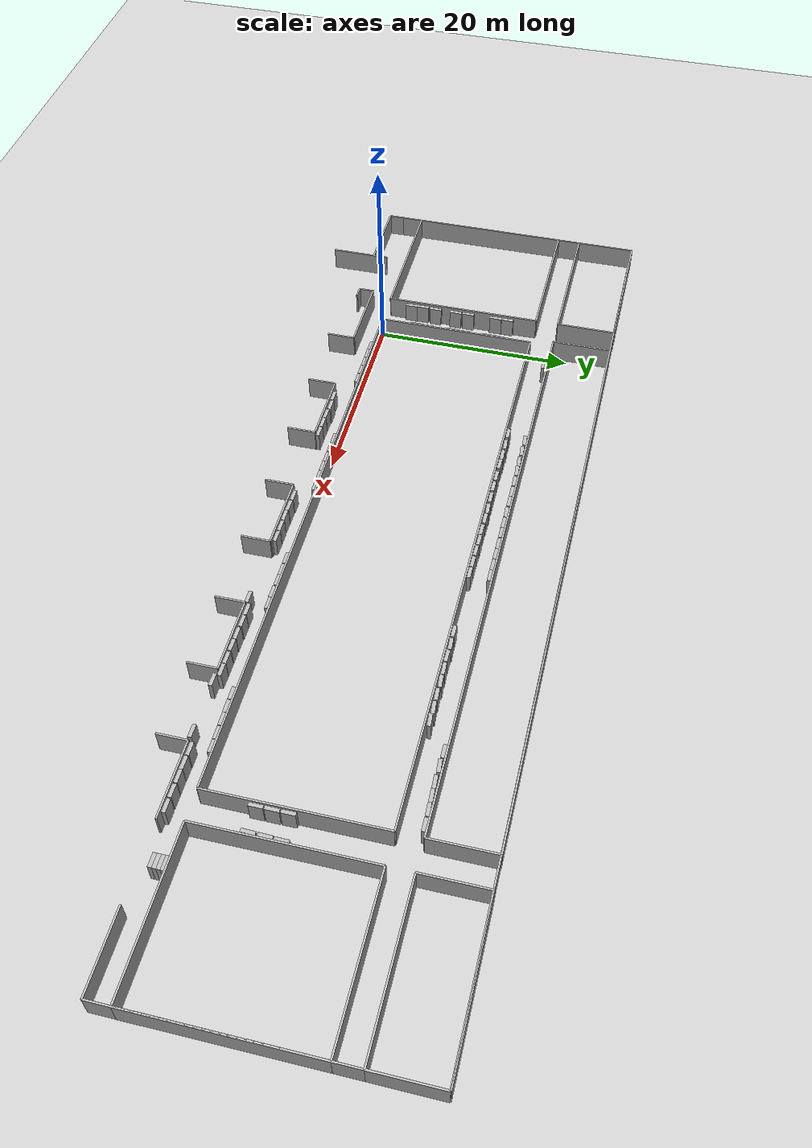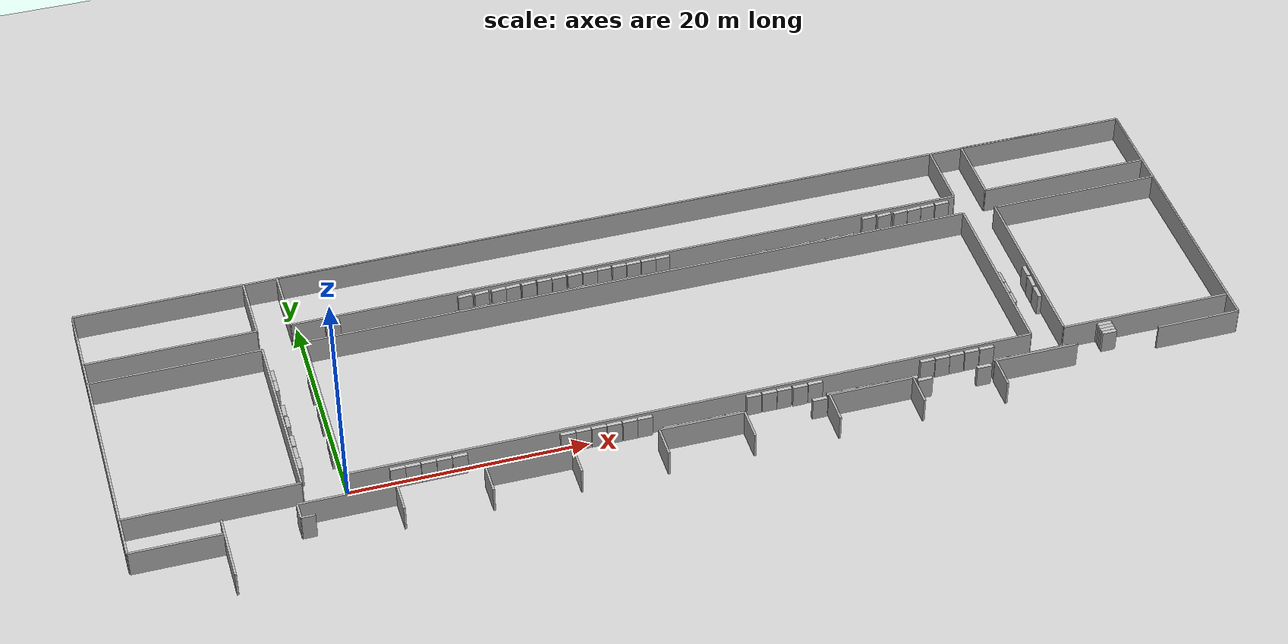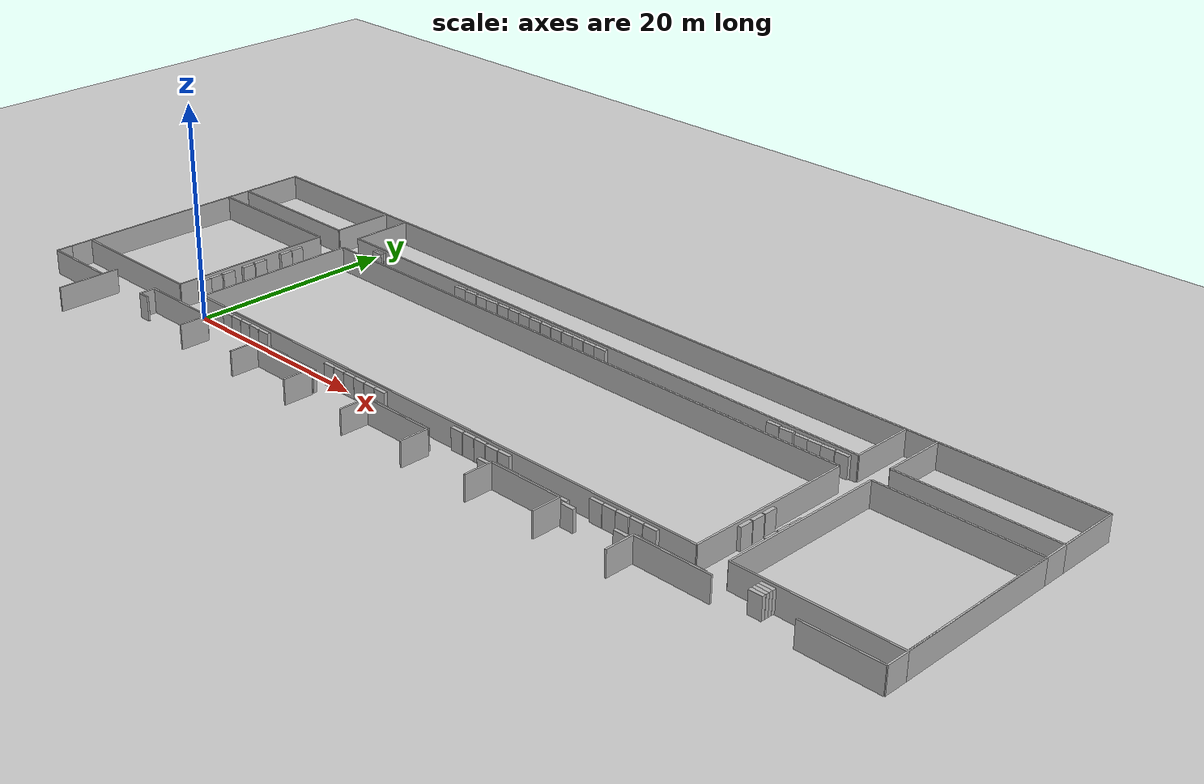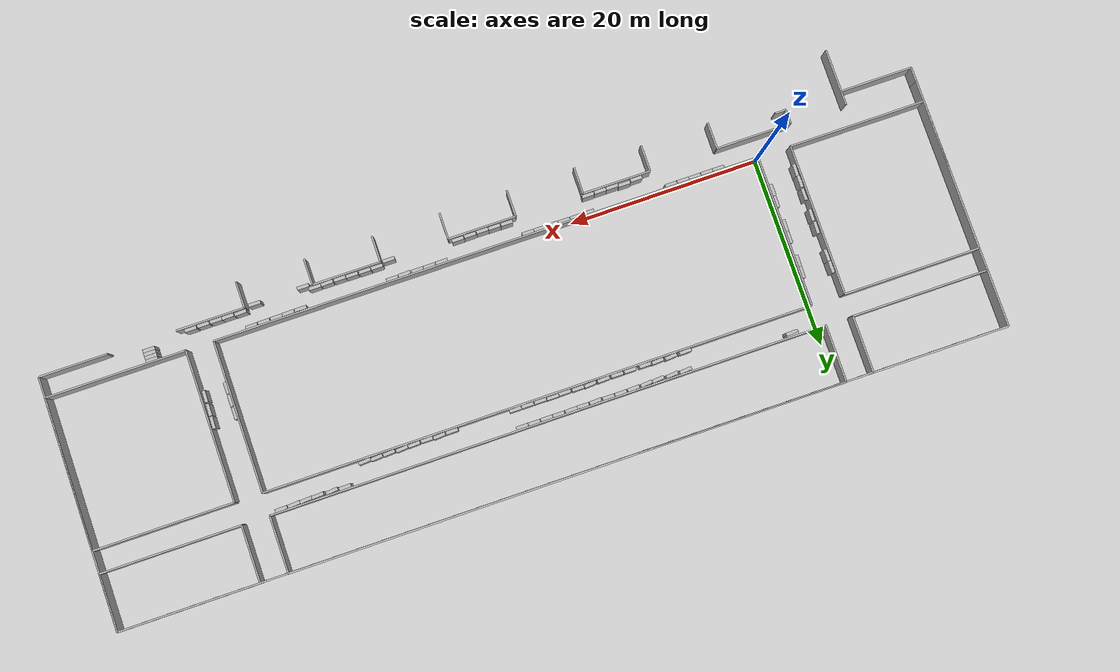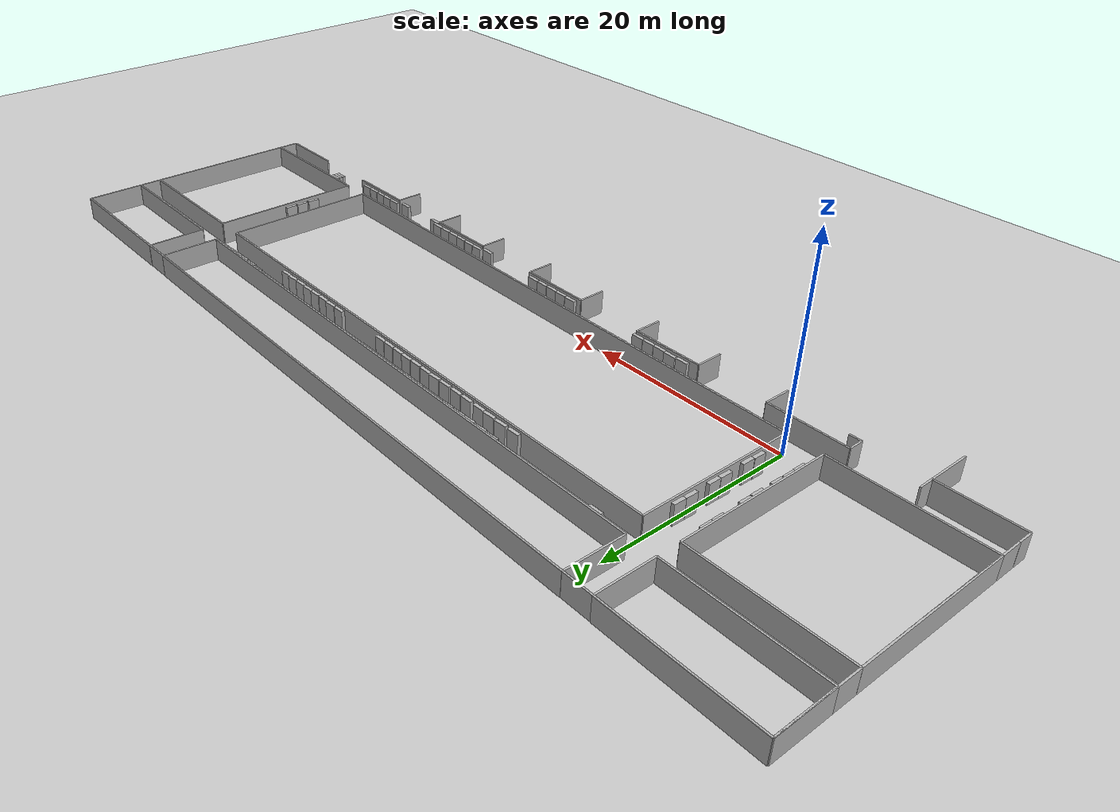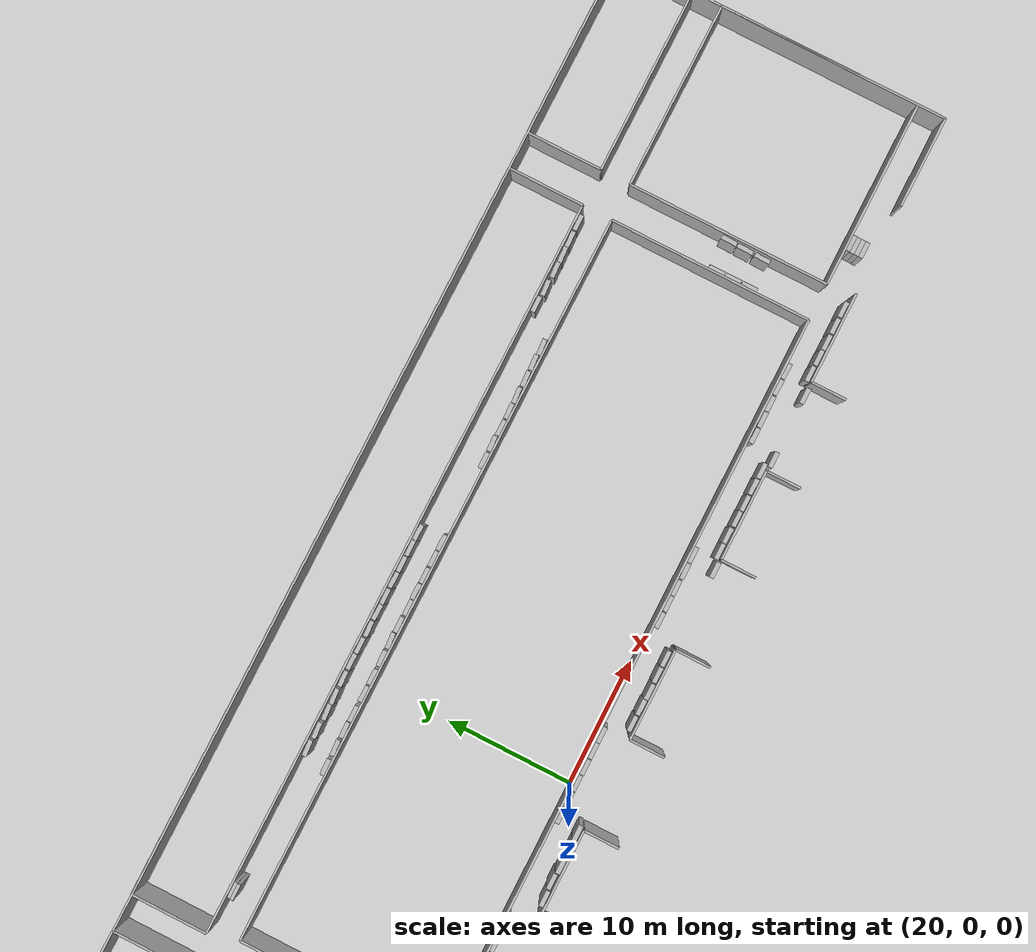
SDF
<sdf version="1.6">
 <world name="default">
  <light name="sun" type="directional">
   <pose>0 0 10 0 -0 0</pose>
   <diffuse>0.8 0.8 0.8 1</diffuse>
   <specular>0.2 0.2 0.2 1</specular>
   <attenuation>
    <range>1000</range>
    <constant>0.9</constant>
    <linear>0.01</linear>
    <quadratic>0.001</quadratic>
   </attenuation>
   <direction>-0.5 0.1 -0.9</direction>
  </light>
  <model name="ground_plane">
   <static>1</static>
   <link name="link">
    <collision name="collision">
     <geometry><plane><normal>0 0 1</normal><size>100 100</size></plane></geometry>
     <surface><friction><ode><mu>100</mu><mu2>50</mu2></ode></friction></surface>
    </collision>
    <visual name="visual">
     <cast_shadows>0</cast_shadows>
     <geometry><plane><normal>0 0 1</normal><size>100 100</size></plane></geometry>
     <material>
      <script><uri>file://media/materials/scripts/gazebo.material</uri><name>Gazebo/Grey</name></script>
     </material>
    </visual>
   </link>
  </model>
  <model name="model_0">
   <pose>0 0 1 0 -0 0</pose>
   <link name="Wall_0">
    <pose>28.988 0 0 0 -0 0</pose>
    <collision name="Wall_0_Collision"><geometry><box><size>57.976 0.169 2.5</size></box></geometry></collision>
    <visual name="Wall_0_Visual"><geometry><box><size>57.976 0.169 2.5</size></box></geometry></visual>
   </link>
   <link name="Wall_1">
    <pose>28.988 16 0 0 -0 0</pose>
    <collision name="Wall_1_Collision"><geometry><box><size>57.976 0.169 2.5</size></box></geometry></collision>
    <visual name="Wall_1_Visual"><geometry><box><size>57.976 0.169 2.5</size></box></geometry></visual>
   </link>
   <link name="Wall_2">
    <pose>0 8 0 0 -0 1.5707</pose>
    <collision name="Wall_2_Collision"><geometry><box><size>16 0.169 2.5</size></box></geometry></collision>
    <visual name="Wall_2_Visual"><geometry><box><size>16 0.169 2.5</size></box></geometry></visual>
   </link>
   <link name="Wall_3">
    <pose>57.976 8 0 0 -0 1.5707</pose>
    <collision name="Wall_3_Collision"><geometry><box><size>16 0.169 2.5</size></box></geometry></collision>
    <visual name="Wall_3_Visual"><geometry><box><size>16 0.169 2.5</size></box></geometry></visual>
   </link>
   <static>1</static>
  </model>
  <model name="model_1">
   <pose>60.9 0 1 0 -0 0</pose>
   <link name="Wall_0">
    <pose>7.369 0 0 0 -0 0</pose>
    <collision name="Wall_0_Collision"><geometry><box><size>14.738 0.169 2.5</size></box></geometry></collision>
    <visual name="Wall_0_Visual"><geometry><box><size>14.738 0.169 2.5</size></box></geometry></visual>
   </link>
   <link name="Wall_1">
    <pose>7.369 16 0 0 -0 0</pose>
    <collision name="Wall_1_Collision"><geometry><box><size>14.738 0.169 2.5</size></box></geometry></collision>
    <visual name="Wall_1_Visual"><geometry><box><size>14.738 0.169 2.5</size></box></geometry></visual>
   </link>
   <link name="Wall_2">
    <pose>0 8 0 0 -0 1.5707</pose>
    <collision name="Wall_2_Collision"><geometry><box><size>16 0.169 2.5</size></box></geometry></collision>
    <visual name="Wall_2_Visual"><geometry><box><size>16 0.169 2.5</size></box></geometry></visual>
   </link>
   <link name="Wall_3">
    <pose>14.738 8 0 0 -0 1.5707</pose>
    <collision name="Wall_3_Collision"><geometry><box><size>16 0.169 2.5</size></box></geometry></collision>
    <visual name="Wall_3_Visual"><geometry><box><size>16 0.169 2.5</size></box></geometry></visual>
   </link>
   <static>1</static>
  </model>
  <model name="model_2">
   <pose>-17.962 0 1 0 -0 0</pose>
   <link name="Wall_0">
    <pose>7.219 0 0 0 -0 0</pose>
    <collision name="Wall_0_Collision"><geometry><box><size>14.438 0.169 2.5</size></box></geometry></collision>
    <visual name="Wall_0_Visual"><geometry><box><size>14.438 0.169 2.5</size></box></geometry></visual>
   </link>
   <link name="Wall_1">
    <pose>7.219 16 0 0 -0 0</pose>
    <collision name="Wall_1_Collision"><geometry><box><size>14.438 0.169 2.5</size></box></geometry></collision>
    <visual name="Wall_1_Visual"><geometry><box><size>14.438 0.169 2.5</size></box></geometry></visual>
   </link>
   <link name="Wall_2">
    <pose>0 8 0 0 -0 1.5707</pose>
    <collision name="Wall_2_Collision"><geometry><box><size>16 0.169 2.5</size></box></geometry></collision>
    <visual name="Wall_2_Visual"><geometry><box><size>16 0.169 2.5</size></box></geometry></visual>
   </link>
   <link name="Wall_3">
    <pose>14.438 8 0 0 -0 1.5707</pose>
    <collision name="Wall_3_Collision"><geometry><box><size>16 0.169 2.5</size></box></geometry></collision>
    <visual name="Wall_3_Visual"><geometry><box><size>16 0.169 2.5</size></box></geometry></visual>
   </link>
   <static>1</static>
  </model>
  <model name="model_3">
   <pose>-17.962 18.362 1 0 -0 0</pose>
   <link name="Wall_0">
    <pose>7.219 0 0 0 -0 0</pose>
    <collision name="Wall_0_Collision"><geometry><box><size>14.438 0.169 2.5</size></box></geometry></collision>
    <visual name="Wall_0_Visual"><geometry><box><size>14.438 0.169 2.5</size></box></geometry></visual>
   </link>
   <link name="Wall_1">
    <pose>7.219 6 0 0 -0 0</pose>
    <collision name="Wall_1_Collision"><geometry><box><size>14.438 0.169 2.5</size></box></geometry></collision>
    <visual name="Wall_1_Visual"><geometry><box><size>14.438 0.169 2.5</size></box></geometry></visual>
   </link>
   <link name="Wall_2">
    <pose>0 3 0 0 -0 1.5707</pose>
    <collision name="Wall_2_Collision"><geometry><box><size>6 0.169 2.5</size></box></geometry></collision>
    <visual name="Wall_2_Visual"><geometry><box><size>6 0.169 2.5</size></box></geometry></visual>
   </link>
   <link name="Wall_3">
    <pose>14.438 3 0 0 -0 1.5707</pose>
    <collision name="Wall_3_Collision"><geometry><box><size>6 0.169 2.5</size></box></geometry></collision>
    <visual name="Wall_3_Visual"><geometry><box><size>6 0.169 2.5</size></box></geometry></visual>
   </link>
   <static>1</static>
  </model>
  <model name="model_4">
   <pose>-0.636 18.362 1 0 -0 0</pose>
   <link name="Wall_0">
    <pose>29.306 0 0 0 -0 0</pose>
    <collision name="Wall_0_Collision"><geometry><box><size>58.612 0.169 2.5</size></box></geometry></collision>
    <visual name="Wall_0_Visual"><geometry><box><size>58.612 0.169 2.5</size></box></geometry></visual>
   </link>
   <link name="Wall_1">
    <pose>29.306 6 0 0 -0 0</pose>
    <collision name="Wall_1_Collision"><geometry><box><size>58.612 0.169 2.5</size></box></geometry></collision>
    <visual name="Wall_1_Visual"><geometry><box><size>58.612 0.169 2.5</size></box></geometry></visual>
   </link>
   <link name="Wall_2">
    <pose>0 3 0 0 -0 1.5707</pose>
    <collision name="Wall_2_Collision"><geometry><box><size>6 0.169 2.5</size></box></geometry></collision>
    <visual name="Wall_2_Visual"><geometry><box><size>6 0.169 2.5</size></box></geometry></visual>
   </link>
   <link name="Wall_3">
    <pose>58.612 3 0 0 -0 1.5707</pose>
    <collision name="Wall_3_Collision"><geometry><box><size>6 0.169 2.5</size></box></geometry></collision>
    <visual name="Wall_3_Visual"><geometry><box><size>6 0.169 2.5</size></box></geometry></visual>
   </link>
   <static>1</static>
  </model>
  <model name="model_5">
   <pose>60.9 18.362 1 0 -0 0</pose>
   <link name="Wall_0">
    <pose>7.369 0 0 0 -0 0</pose>
    <collision name="Wall_0_Collision"><geometry><box><size>14.738 0.169 2.5</size></box></geometry></collision>
    <visual name="Wall_0_Visual"><geometry><box><size>14.738 0.169 2.5</size></box></geometry></visual>
   </link>
   <link name="Wall_1">
    <pose>7.369 6 0 0 -0 0</pose>
    <collision name="Wall_1_Collision"><geometry><box><size>14.738 0.169 2.5</size></box></geometry></collision>
    <visual name="Wall_1_Visual"><geometry><box><size>14.738 0.169 2.5</size></box></geometry></visual>
   </link>
   <link name="Wall_2">
    <pose>0 3 0 0 -0 1.5707</pose>
    <collision name="Wall_2_Collision"><geometry><box><size>6 0.169 2.5</size></box></geometry></collision>
    <visual name="Wall_2_Visual"><geometry><box><size>6 0.169 2.5</size></box></geometry></visual>
   </link>
   <link name="Wall_3">
    <pose>14.738 3 0 0 -0 1.5707</pose>
    <collision name="Wall_3_Collision"><geometry><box><size>6 0.169 2.5</size></box></geometry></collision>
    <visual name="Wall_3_Visual"><geometry><box><size>6 0.169 2.5</size></box></geometry></visual>
   </link>
   <static>1</static>
  </model>
  <model name="model_6">
   <pose>-17.962 -2.202 1 0 -0 0</pose>
   <link name="Wall_0">
    <pose>0 -0.755 0 0 -0 1.5707</pose>
    <collision name="Wall_0_Collision"><geometry><box><size>1.51 0.169 2.5</size></box></geometry></collision>
    <visual name="Wall_0_Visual"><geometry><box><size>1.51 0.169 2.5</size></box></geometry></visual>
   </link>
   <link name="Wall_1">
    <pose>3.809 -1.51 0 0 -0 0</pose>
    <collision name="Wall_1_Collision"><geometry><box><size>7.618 0.169 2.5</size></box></geometry></collision>
    <visual name="Wall_1_Visual"><geometry><box><size>7.618 0.169 2.5</size></box></geometry></visual>
   </link>
   <link name="Wall_2">
    <pose>7.618 -3.005 0 0 -0 1.5707</pose>
    <collision name="Wall_2_Collision"><geometry><box><size>6.01 0.169 2.5</size></box></geometry></collision>
    <visual name="Wall_2_Visual"><geometry><box><size>6.01 0.169 2.5</size></box></geometry></visual>
   </link>
   <link name="Wall_3">
    <pose>13.638 -0.755 0 0 -0 1.5707</pose>
    <collision name="Wall_3_Collision"><geometry><box><size>1.51 0.169 2.5</size></box></geometry></collision>
    <visual name="Wall_3_Visual"><geometry><box><size>1.51 0.169 2.5</size></box></geometry></visual>
   </link>
   <link name="Wall_4">
    <pose>14.214 -1.51 0 0 -0 0</pose>
    <collision name="Wall_4_Collision"><geometry><box><size>1.152 0.169 2.5</size></box></geometry></collision>
    <visual name="Wall_4_Visual"><geometry><box><size>1.152 0.169 2.5</size></box></geometry></visual>
   </link>
   <link name="Wall_5">
    <pose>17.619 0 0 0 -0 0</pose>
    <collision name="Wall_5_Collision"><geometry><box><size>7.962 0.169 2.5</size></box></geometry></collision>
    <visual name="Wall_5_Visual"><geometry><box><size>7.962 0.169 2.5</size></box></geometry></visual>
   </link>
   <link name="Wall_6">
    <pose>21.6 -1.39375 0 0 -0 1.5707</pose>
    <collision name="Wall_6_Collision"><geometry><box><size>2.7875 0.169 2.5</size></box></geometry></collision>
    <visual name="Wall_6_Visual"><geometry><box><size>2.7875 0.169 2.5</size></box></geometry></visual>
   </link>
   <link name="Wall_7">
    <pose>28.8 -1.39375 0 0 -0 1.5707</pose>
    <collision name="Wall_7_Collision"><geometry><box><size>2.7875 0.169 2.5</size></box></geometry></collision>
    <visual name="Wall_7_Visual"><geometry><box><size>2.7875 0.169 2.5</size></box></geometry></visual>
   </link>
   <link name="Wall_8">
    <pose>32.4 0 0 0 -0 0</pose>
    <collision name="Wall_8_Collision"><geometry><box><size>7.2 0.169 2.5</size></box></geometry></collision>
    <visual name="Wall_8_Visual"><geometry><box><size>7.2 0.169 2.5</size></box></geometry></visual>
   </link>
   <link name="Wall_9">
    <pose>36 -1.39375 0 0 -0 1.5707</pose>
    <collision name="Wall_9_Collision"><geometry><box><size>2.7875 0.169 2.5</size></box></geometry></collision>
    <visual name="Wall_9_Visual"><geometry><box><size>2.7875 0.169 2.5</size></box></geometry></visual>
   </link>
   <link name="Wall_10">
    <pose>43.2 -1.39375 0 0 -0 1.5707</pose>
    <collision name="Wall_10_Collision"><geometry><box><size>2.7875 0.169 2.5</size></box></geometry></collision>
    <visual name="Wall_10_Visual"><geometry><box><size>2.7875 0.169 2.5</size></box></geometry></visual>
   </link>
   <link name="Wall_11">
    <pose>46.8 0 0 0 -0 0</pose>
    <collision name="Wall_11_Collision"><geometry><box><size>7.2 0.169 2.5</size></box></geometry></collision>
    <visual name="Wall_11_Visual"><geometry><box><size>7.2 0.169 2.5</size></box></geometry></visual>
   </link>
   <link name="Wall_12">
    <pose>50.4 -1.39375 0 0 -0 1.5707</pose>
    <collision name="Wall_12_Collision"><geometry><box><size>2.7875 0.169 2.5</size></box></geometry></collision>
    <visual name="Wall_12_Visual"><geometry><box><size>2.7875 0.169 2.5</size></box></geometry></visual>
   </link>
   <link name="Wall_13">
    <pose>57.6 -1.39375 0 0 -0 1.5707</pose>
    <collision name="Wall_13_Collision"><geometry><box><size>2.7875 0.169 2.5</size></box></geometry></collision>
    <visual name="Wall_13_Visual"><geometry><box><size>2.7875 0.169 2.5</size></box></geometry></visual>
   </link>
   <link name="Wall_14">
    <pose>61.2 0 0 0 -0 0</pose>
    <collision name="Wall_14_Collision"><geometry><box><size>7.2 0.169 2.5</size></box></geometry></collision>
    <visual name="Wall_14_Visual"><geometry><box><size>7.2 0.169 2.5</size></box></geometry></visual>
   </link>
   <link name="Wall_15">
    <pose>64.8 -1.39375 0 0 -0 1.5707</pose>
    <collision name="Wall_15_Collision"><geometry><box><size>2.7875 0.169 2.5</size></box></geometry></collision>
    <visual name="Wall_15_Visual"><geometry><box><size>2.7875 0.169 2.5</size></box></geometry></visual>
   </link>
   <link name="Wall_16">
    <pose>72 -1.39375 0 0 -0 1.5707</pose>
    <collision name="Wall_16_Collision"><geometry><box><size>2.7875 0.169 2.5</size></box></geometry></collision>
    <visual name="Wall_16_Visual"><geometry><box><size>2.7875 0.169 2.5</size></box></geometry></visual>
   </link>
   <link name="Wall_17">
    <pose>75.6 0 0 0 -0 0</pose>
    <collision name="Wall_17_Collision"><geometry><box><size>7.2 0.169 2.5</size></box></geometry></collision>
    <visual name="Wall_17_Visual"><geometry><box><size>7.2 0.169 2.5</size></box></geometry></visual>
   </link>
   <link name="Wall_18">
    <pose>90 0 0 0 -0 0</pose>
    <collision name="Wall_18_Collision"><geometry><box><size>7.2 0.169 2.5</size></box></geometry></collision>
    <visual name="Wall_18_Visual"><geometry><box><size>7.2 0.169 2.5</size></box></geometry></visual>
   </link>
   <static>1</static>
  </model>
  <model name="model_7">
   <pose>-17.962 -2.202 1 0 -0 0</pose>
   <link name="Wall_0">
    <pose>0 13.27 0 0 -0 1.5707</pose>
    <collision name="Wall_0_Collision"><geometry><box><size>26.54 0.16 2.5</size></box></geometry></collision>
    <visual name="Wall_0_Visual"><geometry><box><size>26.54 0.16 2.5</size></box></geometry></visual>
   </link>
   <link name="Wall_1">
    <pose>46.8 26.54 0 0 -0 0</pose>
    <collision name="Wall_1_Collision"><geometry><box><size>93.6 0.16 2.5</size></box></geometry></collision>
    <visual name="Wall_1_Visual"><geometry><box><size>93.6 0.16 2.5</size></box></geometry></visual>
   </link>
   <link name="Wall_3">
    <pose>93.6 13.27 0 0 -0 1.5707</pose>
    <collision name="Wall_3_Collision"><geometry><box><size>26.54 0.16 2.5</size></box></geometry></collision>
    <visual name="Wall_3_Visual"><geometry><box><size>26.54 0.16 2.5</size></box></geometry></visual>
   </link>
   <static>1</static>
  </model>
  <gravity>0 0 -9.8</gravity>
  <magnetic_field>6e-06 2.3e-05 -4.2e-05</magnetic_field>
  <atmosphere type="adiabatic"/>
  <physics name="default_physics" default="0" type="ode">
   <max_step_size>0.001</max_step_size>
   <real_time_factor>1</real_time_factor>
   <real_time_update_rate>1000</real_time_update_rate>
  </physics>
  <scene><ambient>0.4 0.4 0.4 1</ambient><background>0.7 0.7 0.7 1</background><shadows>1</shadows></scene>
  <audio><device>default</device></audio>
  <spherical_coordinates>
   <surface_model>EARTH_WGS84</surface_model>
   <latitude_deg>0</latitude_deg>
   <longitude_deg>0</longitude_deg>
   <elevation>0</elevation>
   <heading_deg>0</heading_deg>
  </spherical_coordinates>
  <model name="unit_box_clone_1">
   <pose>13.7109 -1.85674 0.999996 0 6e-06 -5.9e-05</pose>
   <link name="link">
    <inertial>
     <mass>1</mass>
     <inertia>
      <ixx>0.166667</ixx>
      <ixy>0</ixy>
      <ixz>0</ixz>
      <iyy>0.166667</iyy>
      <iyz>0</iyz>
      <izz>0.166667</izz>
     </inertia>
    </inertial>
    <collision name="collision"><geometry><box><size>1.25 0.35 2</size></box></geometry></collision>
    <visual name="visual"><geometry><box><size>1.25 0.35 2</size></box></geometry></visual>
   </link>
  </model>
  <model name="unit_box_clone">
   <pose>22.0074 -0.27117 0.999996 -0 -6e-06 -4.9e-05</pose>
   <link name="link">
    <inertial>
     <mass>1</mass>
     <inertia>
      <ixx>0.166667</ixx>
      <ixy>0</ixy>
      <ixz>0</ixz>
      <iyy>0.166667</iyy>
      <iyz>0</iyz>
      <izz>0.166667</izz>
     </inertia>
    </inertial>
    <collision name="collision"><geometry><box><size>1.25 0.35 2</size></box></geometry></collision>
    <visual name="visual"><geometry><box><size>1.25 0.35 2</size></box></geometry></visual>
   </link>
  </model>
  <model name="unit_box_clone_0">
   <pose>26.3118 -1.88538 0.999997 0 -6e-06 -0.000111</pose>
   <link name="link">
    <inertial>
     <mass>1</mass>
     <inertia>
      <ixx>0.166667</ixx>
      <ixy>0</ixy>
      <ixz>0</ixz>
      <iyy>0.166667</iyy>
      <iyz>0</iyz>
      <izz>0.166667</izz>
     </inertia>
    </inertial>
    <collision name="collision"><geometry><box><size>1.25 0.35 2</size></box></geometry></collision>
    <visual name="visual"><geometry><box><size>1.25 0.35 2</size></box></geometry></visual>
   </link>
  </model>
  <model name="unit_box_clone_6">
   <pose>54.6046 -1.902 0.999998 0 3e-06 6.1e-05</pose>
   <link name="link">
    <inertial>
     <mass>1</mass>
     <inertia>
      <ixx>0.166667</ixx>
      <ixy>0</ixy>
      <ixz>0</ixz>
      <iyy>0.166667</iyy>
      <iyz>0</iyz>
      <izz>0.166667</izz>
     </inertia>
    </inertial>
    <collision name="collision"><geometry><box><size>1.25 0.35 2</size></box></geometry></collision>
    <visual name="visual"><geometry><box><size>1.25 0.35 2</size></box></geometry></visual>
   </link>
  </model>
  <model name="unit_box_clone_11_clone_0">
   <pose>56.7525 18.0942 1 0 -0 0.013152</pose>
   <link name="link">
    <inertial>
     <mass>1</mass>
     <inertia>
      <ixx>0.166667</ixx>
      <ixy>0</ixy>
      <ixz>0</ixz>
      <iyy>0.166667</iyy>
      <iyz>0</iyz>
      <izz>0.166667</izz>
     </inertia>
    </inertial>
    <collision name="collision"><geometry><box><size>1.25 0.35 2</size></box></geometry></collision>
    <visual name="visual"><geometry><box><size>1.25 0.35 2</size></box></geometry></visual>
   </link>
  </model>
  <model name="unit_box_clone_11_clone_1">
   <pose>55.4195 18.0661 0.999998 0 4e-06 0.055918</pose>
   <link name="link">
    <inertial>
     <mass>1</mass>
     <inertia>
      <ixx>0.166667</ixx>
      <ixy>0</ixy>
      <ixz>0</ixz>
      <iyy>0.166667</iyy>
      <iyz>0</iyz>
      <izz>0.166667</izz>
     </inertia>
    </inertial>
    <collision name="collision"><geometry><box><size>1.25 0.35 2</size></box></geometry></collision>
    <visual name="visual"><geometry><box><size>1.25 0.35 2</size></box></geometry></visual>
   </link>
  </model>
  <model name="unit_box_clone_11_clone_2">
   <pose>54.1686 18.0364 0.999995 0 2e-06 0.056728</pose>
   <link name="link">
    <inertial>
     <mass>1</mass>
     <inertia>
      <ixx>0.166667</ixx>
      <ixy>0</ixy>
      <ixz>0</ixz>
      <iyy>0.166667</iyy>
      <iyz>0</iyz>
      <izz>0.166667</izz>
     </inertia>
    </inertial>
    <collision name="collision"><geometry><box><size>1.25 0.35 2</size></box></geometry></collision>
    <visual name="visual"><geometry><box><size>1.25 0.35 2</size></box></geometry></visual>
   </link>
  </model>
  <model name="unit_box_clone_11_clone_3">
   <pose>52.9179 18.008 0.999998 0 -3e-06 0.056653</pose>
   <link name="link">
    <inertial>
     <mass>1</mass>
     <inertia>
      <ixx>0.166667</ixx>
      <ixy>0</ixy>
      <ixz>0</ixz>
      <iyy>0.166667</iyy>
      <iyz>0</iyz>
      <izz>0.166667</izz>
     </inertia>
    </inertial>
    <collision name="collision"><geometry><box><size>1.25 0.35 2</size></box></geometry></collision>
    <visual name="visual"><geometry><box><size>1.25 0.35 2</size></box></geometry></visual>
   </link>
  </model>
  <model name="unit_box_clone_11_clone_4">
   <pose>51.4407 18.0271 0.999996 0 2e-06 0.07833</pose>
   <link name="link">
    <inertial>
     <mass>1</mass>
     <inertia>
      <ixx>0.166667</ixx>
      <ixy>0</ixy>
      <ixz>0</ixz>
      <iyy>0.166667</iyy>
      <iyz>0</iyz>
      <izz>0.166667</izz>
     </inertia>
    </inertial>
    <collision name="collision"><geometry><box><size>1.25 0.35 2</size></box></geometry></collision>
    <visual name="visual"><geometry><box><size>1.25 0.35 2</size></box></geometry></visual>
   </link>
  </model>
  <model name="unit_box_clone_11_clone_5">
   <pose>50.0739 18.0916 1 0 -0 0.01582</pose>
   <link name="link">
    <inertial>
     <mass>1</mass>
     <inertia>
      <ixx>0.166667</ixx>
      <ixy>0</ixy>
      <ixz>0</ixz>
      <iyy>0.166667</iyy>
      <iyz>0</iyz>
      <izz>0.166667</izz>
     </inertia>
    </inertial>
    <collision name="collision"><geometry><box><size>1.25 0.35 2</size></box></geometry></collision>
    <visual name="visual"><geometry><box><size>1.25 0.35 2</size></box></geometry></visual>
   </link>
  </model>
  <model name="unit_box_clone_11_clone_6">
   <pose>47.4592 16.3049 1 0 -1e-06 0.0693</pose>
   <link name="link">
    <inertial>
     <mass>1</mass>
     <inertia>
      <ixx>0.166667</ixx>
      <ixy>0</ixy>
      <ixz>0</ixz>
      <iyy>0.166667</iyy>
      <iyz>0</iyz>
      <izz>0.166667</izz>
     </inertia>
    </inertial>
    <collision name="collision"><geometry><box><size>1.25 0.35 2</size></box></geometry></collision>
    <visual name="visual"><geometry><box><size>1.25 0.35 2</size></box></geometry></visual>
   </link>
  </model>
  <model name="unit_box_clone_11_clone_7">
   <pose>46.2039 16.332 1 -1e-06 -0 0.070592</pose>
   <link name="link">
    <inertial>
     <mass>1</mass>
     <inertia>
      <ixx>0.166667</ixx>
      <ixy>0</ixy>
      <ixz>0</ixz>
      <iyy>0.166667</iyy>
      <iyz>0</iyz>
      <izz>0.166667</izz>
     </inertia>
    </inertial>
    <collision name="collision"><geometry><box><size>1.25 0.35 2</size></box></geometry></collision>
    <visual name="visual"><geometry><box><size>1.25 0.35 2</size></box></geometry></visual>
   </link>
  </model>
  <model name="unit_box_clone_11_clone_8">
   <pose>44.8815 16.2979 0.999996 0 2e-06 0.058553</pose>
   <link name="link">
    <inertial>
     <mass>1</mass>
     <inertia>
      <ixx>0.166667</ixx>
      <ixy>0</ixy>
      <ixz>0</ixz>
      <iyy>0.166667</iyy>
      <iyz>0</iyz>
      <izz>0.166667</izz>
     </inertia>
    </inertial>
    <collision name="collision"><geometry><box><size>1.25 0.35 2</size></box></geometry></collision>
    <visual name="visual"><geometry><box><size>1.25 0.35 2</size></box></geometry></visual>
   </link>
  </model>
  <model name="unit_box_clone_11_clone_9">
   <pose>43.5275 16.3169 0.999997 0 6e-06 0.079775</pose>
   <link name="link">
    <inertial>
     <mass>1</mass>
     <inertia>
      <ixx>0.166667</ixx>
      <ixy>0</ixy>
      <ixz>0</ixz>
      <iyy>0.166667</iyy>
      <iyz>0</iyz>
      <izz>0.166667</izz>
     </inertia>
    </inertial>
    <collision name="collision"><geometry><box><size>1.25 0.35 2</size></box></geometry></collision>
    <visual name="visual"><geometry><box><size>1.25 0.35 2</size></box></geometry></visual>
   </link>
  </model>
  <model name="unit_box_clone_11_clone_10">
   <pose>42.2463 16.2883 0.999998 0 -4e-06 0.045982</pose>
   <link name="link">
    <inertial>
     <mass>1</mass>
     <inertia>
      <ixx>0.166667</ixx>
      <ixy>0</ixy>
      <ixz>0</ixz>
      <iyy>0.166667</iyy>
      <iyz>0</iyz>
      <izz>0.166667</izz>
     </inertia>
    </inertial>
    <collision name="collision"><geometry><box><size>1.25 0.35 2</size></box></geometry></collision>
    <visual name="visual"><geometry><box><size>1.25 0.35 2</size></box></geometry></visual>
   </link>
  </model>
  <model name="unit_box_clone_11_clone_11">
   <pose>40.894 16.2613 0.999996 0 6e-06 -1.3e-05</pose>
   <link name="link">
    <inertial>
     <mass>1</mass>
     <inertia>
      <ixx>0.166667</ixx>
      <ixy>0</ixy>
      <ixz>0</ixz>
      <iyy>0.166667</iyy>
      <iyz>0</iyz>
      <izz>0.166667</izz>
     </inertia>
    </inertial>
    <collision name="collision"><geometry><box><size>1.25 0.35 2</size></box></geometry></collision>
    <visual name="visual"><geometry><box><size>1.25 0.35 2</size></box></geometry></visual>
   </link>
  </model>
  <model name="unit_box_clone_11_clone_12">
   <pose>39.5983 16.3008 0.999998 0 3e-06 0.054722</pose>
   <link name="link">
    <inertial>
     <mass>1</mass>
     <inertia>
      <ixx>0.166667</ixx>
      <ixy>0</ixy>
      <ixz>0</ixz>
      <iyy>0.166667</iyy>
      <iyz>0</iyz>
      <izz>0.166667</izz>
     </inertia>
    </inertial>
    <collision name="collision"><geometry><box><size>1.25 0.35 2</size></box></geometry></collision>
    <visual name="visual"><geometry><box><size>1.25 0.35 2</size></box></geometry></visual>
   </link>
  </model>
  <model name="unit_box_clone_11_clone_13">
   <pose>38.2509 16.2695 0.999997 1e-06 5e-06 0.003888</pose>
   <link name="link">
    <inertial>
     <mass>1</mass>
     <inertia>
      <ixx>0.166667</ixx>
      <ixy>0</ixy>
      <ixz>0</ixz>
      <iyy>0.166667</iyy>
      <iyz>0</iyz>
      <izz>0.166667</izz>
     </inertia>
    </inertial>
    <collision name="collision"><geometry><box><size>1.25 0.35 2</size></box></geometry></collision>
    <visual name="visual"><geometry><box><size>1.25 0.35 2</size></box></geometry></visual>
   </link>
  </model>
  <model name="unit_box_clone_11_clone_14">
   <pose>23.711 18.0787 0.999995 0 -2e-06 0.037657</pose>
   <link name="link">
    <inertial>
     <mass>1</mass>
     <inertia>
      <ixx>0.166667</ixx>
      <ixy>0</ixy>
      <ixz>0</ixz>
      <iyy>0.166667</iyy>
      <iyz>0</iyz>
      <izz>0.166667</izz>
     </inertia>
    </inertial>
    <collision name="collision"><geometry><box><size>1.25 0.35 2</size></box></geometry></collision>
    <visual name="visual"><geometry><box><size>1.25 0.35 2</size></box></geometry></visual>
   </link>
  </model>
  <model name="unit_box_clone_11_clone_15">
   <pose>23.6489 16.3031 1 1e-06 0 0.068985</pose>
   <link name="link">
    <inertial>
     <mass>1</mass>
     <inertia>
      <ixx>0.166667</ixx>
      <ixy>0</ixy>
      <ixz>0</ixz>
      <iyy>0.166667</iyy>
      <iyz>0</iyz>
      <izz>0.166667</izz>
     </inertia>
    </inertial>
    <collision name="collision"><geometry><box><size>1.25 0.35 2</size></box></geometry></collision>
    <visual name="visual"><geometry><box><size>1.25 0.35 2</size></box></geometry></visual>
   </link>
  </model>
  <model name="unit_box_clone_11_clone_16">
   <pose>22.3421 18.1015 0.999996 0 6e-06 -4.9e-05</pose>
   <link name="link">
    <inertial>
     <mass>1</mass>
     <inertia>
      <ixx>0.166667</ixx>
      <ixy>0</ixy>
      <ixz>0</ixz>
      <iyy>0.166667</iyy>
      <iyz>0</iyz>
      <izz>0.166667</izz>
     </inertia>
    </inertial>
    <collision name="collision"><geometry><box><size>1.25 0.35 2</size></box></geometry></collision>
    <visual name="visual"><geometry><box><size>1.25 0.35 2</size></box></geometry></visual>
   </link>
  </model>
  <model name="unit_box_clone_11_clone_17">
   <pose>22.2418 16.2769 0.999998 0 -4e-06 0.027685</pose>
   <link name="link">
    <inertial>
     <mass>1</mass>
     <inertia>
      <ixx>0.166667</ixx>
      <ixy>0</ixy>
      <ixz>0</ixz>
      <iyy>0.166667</iyy>
      <iyz>0</iyz>
      <izz>0.166667</izz>
     </inertia>
    </inertial>
    <collision name="collision"><geometry><box><size>1.25 0.35 2</size></box></geometry></collision>
    <visual name="visual"><geometry><box><size>1.25 0.35 2</size></box></geometry></visual>
   </link>
  </model>
  <model name="unit_box_clone_11_clone_18">
   <pose>20.7664 16.2598 0.999996 -0 6e-06 -1.6e-05</pose>
   <link name="link">
    <inertial>
     <mass>1</mass>
     <inertia>
      <ixx>0.166667</ixx>
      <ixy>0</ixy>
      <ixz>0</ixz>
      <iyy>0.166667</iyy>
      <iyz>0</iyz>
      <izz>0.166667</izz>
     </inertia>
    </inertial>
    <collision name="collision"><geometry><box><size>1.25 0.35 2</size></box></geometry></collision>
    <visual name="visual"><geometry><box><size>1.25 0.35 2</size></box></geometry></visual>
   </link>
  </model>
  <model name="unit_box_clone_11_clone_19">
   <pose>21.0428 18.1013 0.999996 0 6e-06 6.1e-05</pose>
   <link name="link">
    <inertial>
     <mass>1</mass>
     <inertia>
      <ixx>0.166667</ixx>
      <ixy>0</ixy>
      <ixz>0</ixz>
      <iyy>0.166667</iyy>
      <iyz>0</iyz>
      <izz>0.166667</izz>
     </inertia>
    </inertial>
    <collision name="collision"><geometry><box><size>1.25 0.35 2</size></box></geometry></collision>
    <visual name="visual"><geometry><box><size>1.25 0.35 2</size></box></geometry></visual>
   </link>
  </model>
  <model name="unit_box_clone_11_clone_20">
   <pose>19.4063 16.2596 0.999996 0 -6e-06 -4.2e-05</pose>
   <link name="link">
    <inertial>
     <mass>1</mass>
     <inertia>
      <ixx>0.166667</ixx>
      <ixy>0</ixy>
      <ixz>0</ixz>
      <iyy>0.166667</iyy>
      <iyz>0</iyz>
      <izz>0.166667</izz>
     </inertia>
    </inertial>
    <collision name="collision"><geometry><box><size>1.25 0.35 2</size></box></geometry></collision>
    <visual name="visual"><geometry><box><size>1.25 0.35 2</size></box></geometry></visual>
   </link>
  </model>
  <model name="unit_box_clone_11_clone_21">
   <pose>17.8003 16.2604 0.999996 0 -2e-06 -8.2e-05</pose>
   <link name="link">
    <inertial>
     <mass>1</mass>
     <inertia>
      <ixx>0.166667</ixx>
      <ixy>0</ixy>
      <ixz>0</ixz>
      <iyy>0.166667</iyy>
      <iyz>0</iyz>
      <izz>0.166667</izz>
     </inertia>
    </inertial>
    <collision name="collision"><geometry><box><size>1.25 0.35 2</size></box></geometry></collision>
    <visual name="visual"><geometry><box><size>1.25 0.35 2</size></box></geometry></visual>
   </link>
  </model>
  <model name="unit_box_clone_11_clone_22">
   <pose>19.6929 18.0816 0.999997 0 -5e-06 0.033077</pose>
   <link name="link">
    <inertial>
     <mass>1</mass>
     <inertia>
      <ixx>0.166667</ixx>
      <ixy>0</ixy>
      <ixz>0</ixz>
      <iyy>0.166667</iyy>
      <iyz>0</iyz>
      <izz>0.166667</izz>
     </inertia>
    </inertial>
    <collision name="collision"><geometry><box><size>1.25 0.35 2</size></box></geometry></collision>
    <visual name="visual"><geometry><box><size>1.25 0.35 2</size></box></geometry></visual>
   </link>
  </model>
  <model name="unit_box_clone_11_clone_23">
   <pose>18.2945 18.0562 0.999998 0 3e-06 0.073835</pose>
   <link name="link">
    <inertial>
     <mass>1</mass>
     <inertia>
      <ixx>0.166667</ixx>
      <ixy>0</ixy>
      <ixz>0</ixz>
      <iyy>0.166667</iyy>
      <iyz>0</iyz>
      <izz>0.166667</izz>
     </inertia>
    </inertial>
    <collision name="collision"><geometry><box><size>1.25 0.35 2</size></box></geometry></collision>
    <visual name="visual"><geometry><box><size>1.25 0.35 2</size></box></geometry></visual>
   </link>
  </model>
  <model name="unit_box_clone_11_clone_24">
   <pose>17.0436 18.0196 0.999997 0 -4e-06 0.073693</pose>
   <link name="link">
    <inertial>
     <mass>1</mass>
     <inertia>
      <ixx>0.166667</ixx>
      <ixy>0</ixy>
      <ixz>0</ixz>
      <iyy>0.166667</iyy>
      <iyz>0</iyz>
      <izz>0.166667</izz>
     </inertia>
    </inertial>
    <collision name="collision"><geometry><box><size>1.25 0.35 2</size></box></geometry></collision>
    <visual name="visual"><geometry><box><size>1.25 0.35 2</size></box></geometry></visual>
   </link>
  </model>
  <model name="unit_box_clone_11_clone_25">
   <pose>16.4932 16.2862 1 0 -0 0.042515</pose>
   <link name="link">
    <inertial>
     <mass>1</mass>
     <inertia>
      <ixx>0.166667</ixx>
      <ixy>0</ixy>
      <ixz>0</ixz>
      <iyy>0.166667</iyy>
      <iyz>0</iyz>
      <izz>0.166667</izz>
     </inertia>
    </inertial>
    <collision name="collision"><geometry><box><size>1.25 0.35 2</size></box></geometry></collision>
    <visual name="visual"><geometry><box><size>1.25 0.35 2</size></box></geometry></visual>
   </link>
  </model>
  <model name="unit_box_clone_11_clone_26">
   <pose>15.5675 18.0384 1 0 -0 0.075277</pose>
   <link name="link">
    <inertial>
     <mass>1</mass>
     <inertia>
      <ixx>0.166667</ixx>
      <ixy>0</ixy>
      <ixz>0</ixz>
      <iyy>0.166667</iyy>
      <iyz>0</iyz>
      <izz>0.166667</izz>
     </inertia>
    </inertial>
    <collision name="collision"><geometry><box><size>1.25 0.35 2</size></box></geometry></collision>
    <visual name="visual"><geometry><box><size>1.25 0.35 2</size></box></geometry></visual>
   </link>
  </model>
  <model name="unit_box_clone_11_clone_27">
   <pose>15.0677 16.2994 1 0 -0 0.060356</pose>
   <link name="link">
    <inertial>
     <mass>1</mass>
     <inertia>
      <ixx>0.166667</ixx>
      <ixy>0</ixy>
      <ixz>0</ixz>
      <iyy>0.166667</iyy>
      <iyz>0</iyz>
      <izz>0.166667</izz>
     </inertia>
    </inertial>
    <collision name="collision"><geometry><box><size>1.25 0.35 2</size></box></geometry></collision>
    <visual name="visual"><geometry><box><size>1.25 0.35 2</size></box></geometry></visual>
   </link>
  </model>
  <model name="unit_box_clone_11_clone_28">
   <pose>14.1457 18.0566 1 0 -0 0.071586</pose>
   <link name="link">
    <inertial>
     <mass>1</mass>
     <inertia>
      <ixx>0.166667</ixx>
      <ixy>0</ixy>
      <ixz>0</ixz>
      <iyy>0.166667</iyy>
      <iyz>0</iyz>
      <izz>0.166667</izz>
     </inertia>
    </inertial>
    <collision name="collision"><geometry><box><size>1.25 0.35 2</size></box></geometry></collision>
    <visual name="visual"><geometry><box><size>1.25 0.35 2</size></box></geometry></visual>
   </link>
  </model>
  <model name="unit_box_clone_11_clone_29">
   <pose>13.536 16.2707 0.999996 -0 -2e-06 0.017689</pose>
   <link name="link">
    <inertial>
     <mass>1</mass>
     <inertia>
      <ixx>0.166667</ixx>
      <ixy>0</ixy>
      <ixz>0</ixz>
      <iyy>0.166667</iyy>
      <iyz>0</iyz>
      <izz>0.166667</izz>
     </inertia>
    </inertial>
    <collision name="collision"><geometry><box><size>1.25 0.35 2</size></box></geometry></collision>
    <visual name="visual"><geometry><box><size>1.25 0.35 2</size></box></geometry></visual>
   </link>
  </model>
  <model name="unit_box_clone_1_clone">
   <pose>6.68095 -0.260339 0.999996 -0 6e-06 4.9e-05</pose>
   <link name="link">
    <inertial>
     <mass>1</mass>
     <inertia>
      <ixx>0.166667</ixx>
      <ixy>0</ixy>
      <ixz>0</ixz>
      <iyy>0.166667</iyy>
      <iyz>0</iyz>
      <izz>0.166667</izz>
     </inertia>
    </inertial>
    <collision name="collision"><geometry><box><size>1.25 0.35 2</size></box></geometry></collision>
    <visual name="visual"><geometry><box><size>1.25 0.35 2</size></box></geometry></visual>
   </link>
  </model>
  <model name="unit_box_clone_1_clone_0">
   <pose>5.39075 -0.263233 0.999998 0 4e-06 0.003933</pose>
   <link name="link">
    <inertial>
     <mass>1</mass>
     <inertia>
      <ixx>0.166667</ixx>
      <ixy>0</ixy>
      <ixz>0</ixz>
      <iyy>0.166667</iyy>
      <iyz>0</iyz>
      <izz>0.166667</izz>
     </inertia>
    </inertial>
    <collision name="collision"><geometry><box><size>1.25 0.35 2</size></box></geometry></collision>
    <visual name="visual"><geometry><box><size>1.25 0.35 2</size></box></geometry></visual>
   </link>
  </model>
  <model name="unit_box_clone_1_clone_1">
   <pose>7.94834 -0.260406 0.999996 -0 2e-06 -7.7e-05</pose>
   <link name="link">
    <inertial>
     <mass>1</mass>
     <inertia>
      <ixx>0.166667</ixx>
      <ixy>0</ixy>
      <ixz>0</ixz>
      <iyy>0.166667</iyy>
      <iyz>0</iyz>
      <izz>0.166667</izz>
     </inertia>
    </inertial>
    <collision name="collision"><geometry><box><size>1.25 0.35 2</size></box></geometry></collision>
    <visual name="visual"><geometry><box><size>1.25 0.35 2</size></box></geometry></visual>
   </link>
  </model>
  <model name="unit_box_clone_1_clone_2">
   <pose>12.3948 -1.94213 1 1e-06 -0 -2.1e-05</pose>
   <link name="link">
    <inertial>
     <mass>1</mass>
     <inertia>
      <ixx>0.166667</ixx>
      <ixy>0</ixy>
      <ixz>0</ixz>
      <iyy>0.166667</iyy>
      <iyz>0</iyz>
      <izz>0.166667</izz>
     </inertia>
    </inertial>
    <collision name="collision"><geometry><box><size>1.25 0.35 2</size></box></geometry></collision>
    <visual name="visual"><geometry><box><size>1.25 0.35 2</size></box></geometry></visual>
   </link>
  </model>
  <model name="unit_box_clone_1_clone_3">
   <pose>14.9959 -1.94196 0.999996 -0 -6e-06 -4.9e-05</pose>
   <link name="link">
    <inertial>
     <mass>1</mass>
     <inertia>
      <ixx>0.166667</ixx>
      <ixy>0</ixy>
      <ixz>0</ixz>
      <iyy>0.166667</iyy>
      <iyz>0</iyz>
      <izz>0.166667</izz>
     </inertia>
    </inertial>
    <collision name="collision"><geometry><box><size>1.25 0.35 2</size></box></geometry></collision>
    <visual name="visual"><geometry><box><size>1.25 0.35 2</size></box></geometry></visual>
   </link>
  </model>
  <model name="unit_box_clone_1_clone_4">
   <pose>16.2794 -1.94101 0.999996 0 -6e-06 -2.4e-05</pose>
   <link name="link">
    <inertial>
     <mass>1</mass>
     <inertia>
      <ixx>0.166667</ixx>
      <ixy>0</ixy>
      <ixz>0</ixz>
      <iyy>0.166667</iyy>
      <iyz>0</iyz>
      <izz>0.166667</izz>
     </inertia>
    </inertial>
    <collision name="collision"><geometry><box><size>1.25 0.35 2</size></box></geometry></collision>
    <visual name="visual"><geometry><box><size>1.25 0.35 2</size></box></geometry></visual>
   </link>
  </model>
  <model name="unit_box_clone_1_clone_5">
   <pose>17.5697 -1.92554 0.999996 0 -6e-06 -4.8e-05</pose>
   <link name="link">
    <inertial>
     <mass>1</mass>
     <inertia>
      <ixx>0.166667</ixx>
      <ixy>0</ixy>
      <ixz>0</ixz>
      <iyy>0.166667</iyy>
      <iyz>0</iyz>
      <izz>0.166667</izz>
     </inertia>
    </inertial>
    <collision name="collision"><geometry><box><size>1.25 0.35 2</size></box></geometry></collision>
    <visual name="visual"><geometry><box><size>1.25 0.35 2</size></box></geometry></visual>
   </link>
  </model>
  <model name="unit_box_clone_1_clone_6">
   <pose>27.6215 -1.91658 0.999996 0 6e-06 2.3e-05</pose>
   <link name="link">
    <inertial>
     <mass>1</mass>
     <inertia>
      <ixx>0.166667</ixx>
      <ixy>0</ixy>
      <ixz>0</ixz>
      <iyy>0.166667</iyy>
      <iyz>0</iyz>
      <izz>0.166667</izz>
     </inertia>
    </inertial>
    <collision name="collision"><geometry><box><size>1.25 0.35 2</size></box></geometry></collision>
    <visual name="visual"><geometry><box><size>1.25 0.35 2</size></box></geometry></visual>
   </link>
  </model>
  <model name="unit_box_clone_1_clone_8">
   <pose>28.8992 -1.9425 1 1e-06 -0 0</pose>
   <link name="link">
    <inertial>
     <mass>1</mass>
     <inertia>
      <ixx>0.166667</ixx>
      <ixy>0</ixy>
      <ixz>0</ixz>
      <iyy>0.166667</iyy>
      <iyz>0</iyz>
      <izz>0.166667</izz>
     </inertia>
    </inertial>
    <collision name="collision"><geometry><box><size>1.25 0.35 2</size></box></geometry></collision>
    <visual name="visual"><geometry><box><size>1.25 0.35 2</size></box></geometry></visual>
   </link>
  </model>
  <model name="unit_box_clone_1_clone_9">
   <pose>30.2126 -1.92359 0.999996 0 6e-06 -1.4e-05</pose>
   <link name="link">
    <inertial>
     <mass>1</mass>
     <inertia>
      <ixx>0.166667</ixx>
      <ixy>0</ixy>
      <ixz>0</ixz>
      <iyy>0.166667</iyy>
      <iyz>0</iyz>
      <izz>0.166667</izz>
     </inertia>
    </inertial>
    <collision name="collision"><geometry><box><size>1.25 0.35 2</size></box></geometry></collision>
    <visual name="visual"><geometry><box><size>1.25 0.35 2</size></box></geometry></visual>
   </link>
  </model>
  <model name="unit_box_clone_1_clone_10">
   <pose>31.5258 -1.90826 0.999998 0 -3e-06 -6.1e-05</pose>
   <link name="link">
    <inertial>
     <mass>1</mass>
     <inertia>
      <ixx>0.166667</ixx>
      <ixy>0</ixy>
      <ixz>0</ixz>
      <iyy>0.166667</iyy>
      <iyz>0</iyz>
      <izz>0.166667</izz>
     </inertia>
    </inertial>
    <collision name="collision"><geometry><box><size>1.25 0.35 2</size></box></geometry></collision>
    <visual name="visual"><geometry><box><size>1.25 0.35 2</size></box></geometry></visual>
   </link>
  </model>
  <model name="unit_box_clone_1_clone_11">
   <pose>20.7352 -0.259681 1 0 0 -0.00018</pose>
   <link name="link">
    <inertial>
     <mass>1</mass>
     <inertia>
      <ixx>0.166667</ixx>
      <ixy>0</ixy>
      <ixz>0</ixz>
      <iyy>0.166667</iyy>
      <iyz>0</iyz>
      <izz>0.166667</izz>
     </inertia>
    </inertial>
    <collision name="collision"><geometry><box><size>1.25 0.35 2</size></box></geometry></collision>
    <visual name="visual"><geometry><box><size>1.25 0.35 2</size></box></geometry></visual>
   </link>
  </model>
  <model name="unit_box_clone_1_clone_12">
   <pose>19.4335 -0.259729 0.999996 0 6e-06 9.4e-05</pose>
   <link name="link">
    <inertial>
     <mass>1</mass>
     <inertia>
      <ixx>0.166667</ixx>
      <ixy>0</ixy>
      <ixz>0</ixz>
      <iyy>0.166667</iyy>
      <iyz>0</iyz>
      <izz>0.166667</izz>
     </inertia>
    </inertial>
    <collision name="collision"><geometry><box><size>1.25 0.35 2</size></box></geometry></collision>
    <visual name="visual"><geometry><box><size>1.25 0.35 2</size></box></geometry></visual>
   </link>
  </model>
  <model name="unit_box_clone_1_clone_13">
   <pose>23.3214 -0.269494 1 -1e-06 0 3.1e-05</pose>
   <link name="link">
    <inertial>
     <mass>1</mass>
     <inertia>
      <ixx>0.166667</ixx>
      <ixy>0</ixy>
      <ixz>0</ixz>
      <iyy>0.166667</iyy>
      <iyz>0</iyz>
      <izz>0.166667</izz>
     </inertia>
    </inertial>
    <collision name="collision"><geometry><box><size>1.25 0.35 2</size></box></geometry></collision>
    <visual name="visual"><geometry><box><size>1.25 0.35 2</size></box></geometry></visual>
   </link>
  </model>
  <model name="unit_box_clone_1_clone_14">
   <pose>18.1558 -0.26028 0.999996 0 6e-06 -3.8e-05</pose>
   <link name="link">
    <inertial>
     <mass>1</mass>
     <inertia>
      <ixx>0.166667</ixx>
      <ixy>0</ixy>
      <ixz>0</ixz>
      <iyy>0.166667</iyy>
      <iyz>0</iyz>
      <izz>0.166667</izz>
     </inertia>
    </inertial>
    <collision name="collision"><geometry><box><size>1.25 0.35 2</size></box></geometry></collision>
    <visual name="visual"><geometry><box><size>1.25 0.35 2</size></box></geometry></visual>
   </link>
  </model>
  <model name="unit_box_clone_1_clone_15">
   <pose>24.5836 -0.2628 0.999996 0 -6e-06 2.4e-05</pose>
   <link name="link">
    <inertial>
     <mass>1</mass>
     <inertia>
      <ixx>0.166667</ixx>
      <ixy>0</ixy>
      <ixz>0</ixz>
      <iyy>0.166667</iyy>
      <iyz>0</iyz>
      <izz>0.166667</izz>
     </inertia>
    </inertial>
    <collision name="collision"><geometry><box><size>1.25 0.35 2</size></box></geometry></collision>
    <visual name="visual"><geometry><box><size>1.25 0.35 2</size></box></geometry></visual>
   </link>
  </model>
  <model name="unit_box_clone_1_clone_20">
   <pose>4.13984 -0.260577 1 -1e-06 0 7e-06</pose>
   <link name="link">
    <inertial>
     <mass>1</mass>
     <inertia>
      <ixx>0.166667</ixx>
      <ixy>0</ixy>
      <ixz>0</ixz>
      <iyy>0.166667</iyy>
      <iyz>0</iyz>
      <izz>0.166667</izz>
     </inertia>
    </inertial>
    <collision name="collision"><geometry><box><size>1.25 0.35 2</size></box></geometry></collision>
    <visual name="visual"><geometry><box><size>1.25 0.35 2</size></box></geometry></visual>
   </link>
  </model>
  <model name="unit_box_clone_1_clone_21">
   <pose>9.23231 -0.2601 0.999996 0 6e-06 -3.9e-05</pose>
   <link name="link">
    <inertial>
     <mass>1</mass>
     <inertia>
      <ixx>0.166667</ixx>
      <ixy>0</ixy>
      <ixz>0</ixz>
      <iyy>0.166667</iyy>
      <iyz>0</iyz>
      <izz>0.166667</izz>
     </inertia>
    </inertial>
    <collision name="collision"><geometry><box><size>1.25 0.35 2</size></box></geometry></collision>
    <visual name="visual"><geometry><box><size>1.25 0.35 2</size></box></geometry></visual>
   </link>
  </model>
  <model name="unit_box_clone_1_clone_7">
   <pose>40.1545 -1.88356 0.999996 -0 -6e-06 -1.3e-05</pose>
   <link name="link">
    <inertial>
     <mass>1</mass>
     <inertia>
      <ixx>0.166667</ixx>
      <ixy>0</ixy>
      <ixz>0</ixz>
      <iyy>0.166667</iyy>
      <iyz>0</iyz>
      <izz>0.166667</izz>
     </inertia>
    </inertial>
    <collision name="collision"><geometry><box><size>1.25 0.35 2</size></box></geometry></collision>
    <visual name="visual"><geometry><box><size>1.25 0.35 2</size></box></geometry></visual>
   </link>
  </model>
  <model name="unit_box_clone_1_clone_16">
   <pose>41.444 -1.88485 0.999996 -0 2e-06 -8.6e-05</pose>
   <link name="link">
    <inertial>
     <mass>1</mass>
     <inertia>
      <ixx>0.166667</ixx>
      <ixy>0</ixy>
      <ixz>0</ixz>
      <iyy>0.166667</iyy>
      <iyz>0</iyz>
      <izz>0.166667</izz>
     </inertia>
    </inertial>
    <collision name="collision"><geometry><box><size>1.25 0.35 2</size></box></geometry></collision>
    <visual name="visual"><geometry><box><size>1.25 0.35 2</size></box></geometry></visual>
   </link>
  </model>
  <model name="unit_box_clone_1_clone_17">
   <pose>42.7968 -1.91646 1 -1e-06 -0 1e-05</pose>
   <link name="link">
    <inertial>
     <mass>1</mass>
     <inertia>
      <ixx>0.166667</ixx>
      <ixy>0</ixy>
      <ixz>0</ixz>
      <iyy>0.166667</iyy>
      <iyz>0</iyz>
      <izz>0.166667</izz>
     </inertia>
    </inertial>
    <collision name="collision"><geometry><box><size>1.25 0.35 2</size></box></geometry></collision>
    <visual name="visual"><geometry><box><size>1.25 0.35 2</size></box></geometry></visual>
   </link>
  </model>
  <model name="unit_box_clone_1_clone_18">
   <pose>44.0856 -1.94196 0.999996 0 -6e-06 5.5e-05</pose>
   <link name="link">
    <inertial>
     <mass>1</mass>
     <inertia>
      <ixx>0.166667</ixx>
      <ixy>0</ixy>
      <ixz>0</ixz>
      <iyy>0.166667</iyy>
      <iyz>0</iyz>
      <izz>0.166667</izz>
     </inertia>
    </inertial>
    <collision name="collision"><geometry><box><size>1.25 0.35 2</size></box></geometry></collision>
    <visual name="visual"><geometry><box><size>1.25 0.35 2</size></box></geometry></visual>
   </link>
  </model>
  <model name="unit_box_clone_1_clone_19">
   <pose>45.4366 -1.94203 0.999996 0 6e-06 -3.6e-05</pose>
   <link name="link">
    <inertial>
     <mass>1</mass>
     <inertia>
      <ixx>0.166667</ixx>
      <ixy>0</ixy>
      <ixz>0</ixz>
      <iyy>0.166667</iyy>
      <iyz>0</iyz>
      <izz>0.166667</izz>
     </inertia>
    </inertial>
    <collision name="collision"><geometry><box><size>1.25 0.35 2</size></box></geometry></collision>
    <visual name="visual"><geometry><box><size>1.25 0.35 2</size></box></geometry></visual>
   </link>
  </model>
  <model name="unit_box_clone_1_clone_22">
   <pose>46.7262 -1.94249 1 0 0 -4.8e-05</pose>
   <link name="link">
    <inertial>
     <mass>1</mass>
     <inertia>
      <ixx>0.166667</ixx>
      <ixy>0</ixy>
      <ixz>0</ixz>
      <iyy>0.166667</iyy>
      <iyz>0</iyz>
      <izz>0.166667</izz>
     </inertia>
    </inertial>
    <collision name="collision"><geometry><box><size>1.25 0.35 2</size></box></geometry></collision>
    <visual name="visual"><geometry><box><size>1.25 0.35 2</size></box></geometry></visual>
   </link>
  </model>
  <model name="unit_box_clone_1_clone_23">
   <pose>33.7971 -0.269884 1 -1e-06 -0 4e-06</pose>
   <link name="link">
    <inertial>
     <mass>1</mass>
     <inertia>
      <ixx>0.166667</ixx>
      <ixy>0</ixy>
      <ixz>0</ixz>
      <iyy>0.166667</iyy>
      <iyz>0</iyz>
      <izz>0.166667</izz>
     </inertia>
    </inertial>
    <collision name="collision"><geometry><box><size>1.25 0.35 2</size></box></geometry></collision>
    <visual name="visual"><geometry><box><size>1.25 0.35 2</size></box></geometry></visual>
   </link>
  </model>
  <model name="unit_box_clone_1_clone_24">
   <pose>35.1254 -0.260039 1 -1e-06 0 1.8e-05</pose>
   <link name="link">
    <inertial>
     <mass>1</mass>
     <inertia>
      <ixx>0.166667</ixx>
      <ixy>0</ixy>
      <ixz>0</ixz>
      <iyy>0.166667</iyy>
      <iyz>0</iyz>
      <izz>0.166667</izz>
     </inertia>
    </inertial>
    <collision name="collision"><geometry><box><size>1.25 0.35 2</size></box></geometry></collision>
    <visual name="visual"><geometry><box><size>1.25 0.35 2</size></box></geometry></visual>
   </link>
  </model>
  <model name="unit_box_clone_1_clone_25">
   <pose>36.3934 -0.260366 0.999996 0 -6e-06 4e-05</pose>
   <link name="link">
    <inertial>
     <mass>1</mass>
     <inertia>
      <ixx>0.166667</ixx>
      <ixy>0</ixy>
      <ixz>0</ixz>
      <iyy>0.166667</iyy>
      <iyz>0</iyz>
      <izz>0.166667</izz>
     </inertia>
    </inertial>
    <collision name="collision"><geometry><box><size>1.25 0.35 2</size></box></geometry></collision>
    <visual name="visual"><geometry><box><size>1.25 0.35 2</size></box></geometry></visual>
   </link>
  </model>
  <model name="unit_box_clone_1_clone_26">
   <pose>37.7551 -0.304386 0.999996 0 6e-06 4.3e-05</pose>
   <link name="link">
    <inertial>
     <mass>1</mass>
     <inertia>
      <ixx>0.166667</ixx>
      <ixy>0</ixy>
      <ixz>0</ixz>
      <iyy>0.166667</iyy>
      <iyz>0</iyz>
      <izz>0.166667</izz>
     </inertia>
    </inertial>
    <collision name="collision"><geometry><box><size>1.25 0.35 2</size></box></geometry></collision>
    <visual name="visual"><geometry><box><size>1.25 0.35 2</size></box></geometry></visual>
   </link>
  </model>
  <model name="unit_box_clone_1_clone_27">
   <pose>39.0548 -0.260579 0.999998 0 -3e-06 -2.9e-05</pose>
   <link name="link">
    <inertial>
     <mass>1</mass>
     <inertia>
      <ixx>0.166667</ixx>
      <ixy>0</ixy>
      <ixz>0</ixz>
      <iyy>0.166667</iyy>
      <iyz>0</iyz>
      <izz>0.166667</izz>
     </inertia>
    </inertial>
    <collision name="collision"><geometry><box><size>1.25 0.35 2</size></box></geometry></collision>
    <visual name="visual"><geometry><box><size>1.25 0.35 2</size></box></geometry></visual>
   </link>
  </model>
  <model name="unit_box_clone_1_clone_28">
   <pose>48.7566 -0.324881 0.999996 0 -6e-06 1.9e-05</pose>
   <link name="link">
    <inertial>
     <mass>1</mass>
     <inertia>
      <ixx>0.166667</ixx>
      <ixy>0</ixy>
      <ixz>0</ixz>
      <iyy>0.166667</iyy>
      <iyz>0</iyz>
      <izz>0.166667</izz>
     </inertia>
    </inertial>
    <collision name="collision"><geometry><box><size>1.25 0.35 2</size></box></geometry></collision>
    <visual name="visual"><geometry><box><size>1.25 0.35 2</size></box></geometry></visual>
   </link>
  </model>
  <model name="unit_box_clone_1_clone_29">
   <pose>50.0592 -0.326024 0.999996 0 -6e-06 4.6e-05</pose>
   <link name="link">
    <inertial>
     <mass>1</mass>
     <inertia>
      <ixx>0.166667</ixx>
      <ixy>0</ixy>
      <ixz>0</ixz>
      <iyy>0.166667</iyy>
      <iyz>0</iyz>
      <izz>0.166667</izz>
     </inertia>
    </inertial>
    <collision name="collision"><geometry><box><size>1.25 0.35 2</size></box></geometry></collision>
    <visual name="visual"><geometry><box><size>1.25 0.35 2</size></box></geometry></visual>
   </link>
  </model>
  <model name="unit_box_clone_1_clone_30">
   <pose>51.3296 -0.296932 0.999996 0 6e-06 -3.6e-05</pose>
   <link name="link">
    <inertial>
     <mass>1</mass>
     <inertia>
      <ixx>0.166667</ixx>
      <ixy>0</ixy>
      <ixz>0</ixz>
      <iyy>0.166667</iyy>
      <iyz>0</iyz>
      <izz>0.166667</izz>
     </inertia>
    </inertial>
    <collision name="collision"><geometry><box><size>1.25 0.35 2</size></box></geometry></collision>
    <visual name="visual"><geometry><box><size>1.25 0.35 2</size></box></geometry></visual>
   </link>
  </model>
  <model name="unit_box_clone_1_clone_31">
   <pose>52.6602 -0.26924 0.999996 -0 -2e-06 8.4e-05</pose>
   <link name="link">
    <inertial>
     <mass>1</mass>
     <inertia>
      <ixx>0.166667</ixx>
      <ixy>0</ixy>
      <ixz>0</ixz>
      <iyy>0.166667</iyy>
      <iyz>0</iyz>
      <izz>0.166667</izz>
     </inertia>
    </inertial>
    <collision name="collision"><geometry><box><size>1.25 0.35 2</size></box></geometry></collision>
    <visual name="visual"><geometry><box><size>1.25 0.35 2</size></box></geometry></visual>
   </link>
  </model>
  <model name="unit_box_clone_1_clone_32">
   <pose>53.9646 -0.259585 1 0 -0 0.000135</pose>
   <link name="link">
    <inertial>
     <mass>1</mass>
     <inertia>
      <ixx>0.166667</ixx>
      <ixy>0</ixy>
      <ixz>0</ixz>
      <iyy>0.166667</iyy>
      <iyz>0</iyz>
      <izz>0.166667</izz>
     </inertia>
    </inertial>
    <collision name="collision"><geometry><box><size>1.25 0.35 2</size></box></geometry></collision>
    <visual name="visual"><geometry><box><size>1.25 0.35 2</size></box></geometry></visual>
   </link>
  </model>
  <model name="unit_box_clone_1_clone_33">
   <pose>55.9279 -1.93098 0.999996 0 -6e-06 1.8e-05</pose>
   <link name="link">
    <inertial>
     <mass>1</mass>
     <inertia>
      <ixx>0.166667</ixx>
      <ixy>0</ixy>
      <ixz>0</ixz>
      <iyy>0.166667</iyy>
      <iyz>0</iyz>
      <izz>0.166667</izz>
     </inertia>
    </inertial>
    <collision name="collision"><geometry><box><size>1.25 0.35 2</size></box></geometry></collision>
    <visual name="visual"><geometry><box><size>1.25 0.35 2</size></box></geometry></visual>
   </link>
  </model>
  <model name="unit_box_clone_1_clone_34">
   <pose>57.191 -1.94229 1 0 -0 0.000143</pose>
   <link name="link">
    <inertial>
     <mass>1</mass>
     <inertia>
      <ixx>0.166667</ixx>
      <ixy>0</ixy>
      <ixz>0</ixz>
      <iyy>0.166667</iyy>
      <iyz>0</iyz>
      <izz>0.166667</izz>
     </inertia>
    </inertial>
    <collision name="collision"><geometry><box><size>1.25 0.35 2</size></box></geometry></collision>
    <visual name="visual"><geometry><box><size>1.25 0.35 2</size></box></geometry></visual>
   </link>
  </model>
  <model name="unit_box_clone_1_clone_35">
   <pose>58.515 -1.94236 0.999998 -0 -4e-06 -0.000153</pose>
   <link name="link">
    <inertial>
     <mass>1</mass>
     <inertia>
      <ixx>0.166667</ixx>
      <ixy>0</ixy>
      <ixz>0</ixz>
      <iyy>0.166667</iyy>
      <iyz>0</iyz>
      <izz>0.166667</izz>
     </inertia>
    </inertial>
    <collision name="collision"><geometry><box><size>1.25 0.35 2</size></box></geometry></collision>
    <visual name="visual"><geometry><box><size>1.25 0.35 2</size></box></geometry></visual>
   </link>
  </model>
  <model name="unit_box_clone_1_clone_36">
   <pose>59.8662 -1.93541 1 -1e-06 0 -3e-06</pose>
   <link name="link">
    <inertial>
     <mass>1</mass>
     <inertia>
      <ixx>0.166667</ixx>
      <ixy>0</ixy>
      <ixz>0</ixz>
      <iyy>0.166667</iyy>
      <iyz>0</iyz>
      <izz>0.166667</izz>
     </inertia>
    </inertial>
    <collision name="collision"><geometry><box><size>1.25 0.35 2</size></box></geometry></collision>
    <visual name="visual"><geometry><box><size>1.25 0.35 2</size></box></geometry></visual>
   </link>
  </model>
  <model name="unit_box_clone_1_clone_37">
   <pose>64.4557 -0.259713 0.999996 0 -2e-06 -9.7e-05</pose>
   <link name="link">
    <inertial>
     <mass>1</mass>
     <inertia>
      <ixx>0.166667</ixx>
      <ixy>0</ixy>
      <ixz>0</ixz>
      <iyy>0.166667</iyy>
      <iyz>0</iyz>
      <izz>0.166667</izz>
     </inertia>
    </inertial>
    <collision name="collision"><geometry><box><size>1.25 0.35 2</size></box></geometry></collision>
    <visual name="visual"><geometry><box><size>1.25 0.35 2</size></box></geometry></visual>
   </link>
  </model>
  <model name="unit_box_clone_1_clone_38">
   <pose>64.4499 -0.609721 0.999996 0 -2e-06 -9.5e-05</pose>
   <link name="link">
    <inertial>
     <mass>1</mass>
     <inertia>
      <ixx>0.166667</ixx>
      <ixy>0</ixy>
      <ixz>0</ixz>
      <iyy>0.166667</iyy>
      <iyz>0</iyz>
      <izz>0.166667</izz>
     </inertia>
    </inertial>
    <collision name="collision"><geometry><box><size>1.25 0.35 2</size></box></geometry></collision>
    <visual name="visual"><geometry><box><size>1.25 0.35 2</size></box></geometry></visual>
   </link>
  </model>
  <model name="unit_box_clone_1_clone_39">
   <pose>64.4459 -0.95993 0.999996 -0 -2e-06 2.4e-05</pose>
   <link name="link">
    <inertial>
     <mass>1</mass>
     <inertia>
      <ixx>0.166667</ixx>
      <ixy>0</ixy>
      <ixz>0</ixz>
      <iyy>0.166667</iyy>
      <iyz>0</iyz>
      <izz>0.166667</izz>
     </inertia>
    </inertial>
    <collision name="collision"><geometry><box><size>1.25 0.35 2</size></box></geometry></collision>
    <visual name="visual"><geometry><box><size>1.25 0.35 2</size></box></geometry></visual>
   </link>
  </model>
  <model name="unit_box_clone_1_clone_40">
   <pose>64.4382 -1.31008 1 -1e-06 -0 -6e-06</pose>
   <link name="link">
    <inertial>
     <mass>1</mass>
     <inertia>
      <ixx>0.166667</ixx>
      <ixy>0</ixy>
      <ixz>0</ixz>
      <iyy>0.166667</iyy>
      <iyz>0</iyz>
      <izz>0.166667</izz>
     </inertia>
    </inertial>
    <collision name="collision"><geometry><box><size>1.25 0.35 2</size></box></geometry></collision>
    <visual name="visual"><geometry><box><size>1.25 0.35 2</size></box></geometry></visual>
   </link>
  </model>
  <model name="unit_box_clone_1_clone_41">
   <pose>25.0388 18.0857 1 -0 1e-06 -0.023169</pose>
   <link name="link">
    <inertial>
     <mass>1</mass>
     <inertia>
      <ixx>0.166667</ixx>
      <ixy>0</ixy>
      <ixz>0</ixz>
      <iyy>0.166667</iyy>
      <iyz>0</iyz>
      <izz>0.166667</izz>
     </inertia>
    </inertial>
    <collision name="collision"><geometry><box><size>1.25 0.35 2</size></box></geometry></collision>
    <visual name="visual"><geometry><box><size>1.25 0.35 2</size></box></geometry></visual>
   </link>
  </model>
  <model name="unit_box_clone_1_clone_42">
   <pose>26.2926 18.1022 0.99999 -0 2e-06 -0.000423</pose>
   <link name="link">
    <inertial>
     <mass>1</mass>
     <inertia>
      <ixx>0.166667</ixx>
      <ixy>0</ixy>
      <ixz>0</ixz>
      <iyy>0.166667</iyy>
      <iyz>0</iyz>
      <izz>0.166667</izz>
     </inertia>
    </inertial>
    <collision name="collision"><geometry><box><size>1.25 0.35 2</size></box></geometry></collision>
    <visual name="visual"><geometry><box><size>1.25 0.35 2</size></box></geometry></visual>
   </link>
  </model>
  <model name="unit_box_clone_1_clone_43">
   <pose>27.6286 18.1024 0.999996 -0 2e-06 -7.7e-05</pose>
   <link name="link">
    <inertial>
     <mass>1</mass>
     <inertia>
      <ixx>0.166667</ixx>
      <ixy>0</ixy>
      <ixz>0</ixz>
      <iyy>0.166667</iyy>
      <iyz>0</iyz>
      <izz>0.166667</izz>
     </inertia>
    </inertial>
    <collision name="collision"><geometry><box><size>1.25 0.35 2</size></box></geometry></collision>
    <visual name="visual"><geometry><box><size>1.25 0.35 2</size></box></geometry></visual>
   </link>
  </model>
  <model name="unit_box_clone_1_clone_44">
   <pose>28.9017 18.1019 0.999996 -0 -2e-06 7.2e-05</pose>
   <link name="link">
    <inertial>
     <mass>1</mass>
     <inertia>
      <ixx>0.166667</ixx>
      <ixy>0</ixy>
      <ixz>0</ixz>
      <iyy>0.166667</iyy>
      <iyz>0</iyz>
      <izz>0.166667</izz>
     </inertia>
    </inertial>
    <collision name="collision"><geometry><box><size>1.25 0.35 2</size></box></geometry></collision>
    <visual name="visual"><geometry><box><size>1.25 0.35 2</size></box></geometry></visual>
   </link>
  </model>
  <model name="unit_box_clone_1_clone_45">
   <pose>30.2063 18.1022 1 0 -0 3e-06</pose>
   <link name="link">
    <inertial>
     <mass>1</mass>
     <inertia>
      <ixx>0.166667</ixx>
      <ixy>0</ixy>
      <ixz>0</ixz>
      <iyy>0.166667</iyy>
      <iyz>0</iyz>
      <izz>0.166667</izz>
     </inertia>
    </inertial>
    <collision name="collision"><geometry><box><size>1.25 0.35 2</size></box></geometry></collision>
    <visual name="visual"><geometry><box><size>1.25 0.35 2</size></box></geometry></visual>
   </link>
  </model>
  <model name="unit_box_clone_1_clone_46">
   <pose>24.9483 16.2925 1 -1e-06 0 2e-06</pose>
   <link name="link">
    <inertial>
     <mass>1</mass>
     <inertia>
      <ixx>0.166667</ixx>
      <ixy>0</ixy>
      <ixz>0</ixz>
      <iyy>0.166667</iyy>
      <iyz>0</iyz>
      <izz>0.166667</izz>
     </inertia>
    </inertial>
    <collision name="collision"><geometry><box><size>1.25 0.35 2</size></box></geometry></collision>
    <visual name="visual"><geometry><box><size>1.25 0.35 2</size></box></geometry></visual>
   </link>
  </model>
  <model name="unit_box_clone_1_clone_47">
   <pose>26.3335 16.2599 0.999996 0 6e-06 -6.8e-05</pose>
   <link name="link">
    <inertial>
     <mass>1</mass>
     <inertia>
      <ixx>0.166667</ixx>
      <ixy>0</ixy>
      <ixz>0</ixz>
      <iyy>0.166667</iyy>
      <iyz>0</iyz>
      <izz>0.166667</izz>
     </inertia>
    </inertial>
    <collision name="collision"><geometry><box><size>1.25 0.35 2</size></box></geometry></collision>
    <visual name="visual"><geometry><box><size>1.25 0.35 2</size></box></geometry></visual>
   </link>
  </model>
  <model name="unit_box_clone_1_clone_48">
   <pose>27.6264 16.2924 1 1e-06 0 -8e-06</pose>
   <link name="link">
    <inertial>
     <mass>1</mass>
     <inertia>
      <ixx>0.166667</ixx>
      <ixy>0</ixy>
      <ixz>0</ixz>
      <iyy>0.166667</iyy>
      <iyz>0</iyz>
      <izz>0.166667</izz>
     </inertia>
    </inertial>
    <collision name="collision"><geometry><box><size>1.25 0.35 2</size></box></geometry></collision>
    <visual name="visual"><geometry><box><size>1.25 0.35 2</size></box></geometry></visual>
   </link>
  </model>
  <model name="unit_box_clone_1_clone_49">
   <pose>28.9216 16.2603 0.999998 -0 3e-06 -1.3e-05</pose>
   <link name="link">
    <inertial>
     <mass>1</mass>
     <inertia>
      <ixx>0.166667</ixx>
      <ixy>0</ixy>
      <ixz>0</ixz>
      <iyy>0.166667</iyy>
      <iyz>0</iyz>
      <izz>0.166667</izz>
     </inertia>
    </inertial>
    <collision name="collision"><geometry><box><size>1.25 0.35 2</size></box></geometry></collision>
    <visual name="visual"><geometry><box><size>1.25 0.35 2</size></box></geometry></visual>
   </link>
  </model>
  <model name="unit_box_clone_1_clone_50">
   <pose>30.2756 16.2598 0.999998 -0 -3e-06 -6.5e-05</pose>
   <link name="link">
    <inertial>
     <mass>1</mass>
     <inertia>
      <ixx>0.166667</ixx>
      <ixy>0</ixy>
      <ixz>0</ixz>
      <iyy>0.166667</iyy>
      <iyz>0</iyz>
      <izz>0.166667</izz>
     </inertia>
    </inertial>
    <collision name="collision"><geometry><box><size>1.25 0.35 2</size></box></geometry></collision>
    <visual name="visual"><geometry><box><size>1.25 0.35 2</size></box></geometry></visual>
   </link>
  </model>
  <model name="unit_box_clone_1_clone_51">
   <pose>31.5704 16.2602 0.999998 -0 -3e-06 -3.6e-05</pose>
   <link name="link">
    <inertial>
     <mass>1</mass>
     <inertia>
      <ixx>0.166667</ixx>
      <ixy>0</ixy>
      <ixz>0</ixz>
      <iyy>0.166667</iyy>
      <iyz>0</iyz>
      <izz>0.166667</izz>
     </inertia>
    </inertial>
    <collision name="collision"><geometry><box><size>1.25 0.35 2</size></box></geometry></collision>
    <visual name="visual"><geometry><box><size>1.25 0.35 2</size></box></geometry></visual>
   </link>
  </model>
  <model name="unit_box_clone_1_clone_52">
   <pose>31.4667 18.1023 1 0 -0 0.000257</pose>
   <link name="link">
    <inertial>
     <mass>1</mass>
     <inertia>
      <ixx>0.166667</ixx>
      <ixy>0</ixy>
      <ixz>0</ixz>
      <iyy>0.166667</iyy>
      <iyz>0</iyz>
      <izz>0.166667</izz>
     </inertia>
    </inertial>
    <collision name="collision"><geometry><box><size>1.25 0.35 2</size></box></geometry></collision>
    <visual name="visual"><geometry><box><size>1.25 0.35 2</size></box></geometry></visual>
   </link>
  </model>
  <model name="unit_box_clone_1_clone_53">
   <pose>38.8134 -2.17996 0.999996 -0 -2e-06 7.5e-05</pose>
   <link name="link">
    <inertial>
     <mass>1</mass>
     <inertia>
      <ixx>0.166667</ixx>
      <ixy>0</ixy>
      <ixz>0</ixz>
      <iyy>0.166667</iyy>
      <iyz>0</iyz>
      <izz>0.166667</izz>
     </inertia>
    </inertial>
    <collision name="collision"><geometry><box><size>1.25 0.35 2</size></box></geometry></collision>
    <visual name="visual"><geometry><box><size>1.25 0.35 2</size></box></geometry></visual>
   </link>
  </model>
  <model name="unit_box_clone_1_clone_54">
   <pose>47.8326 -2.34908 1 1e-06 -0 -9e-06</pose>
   <link name="link">
    <inertial>
     <mass>1</mass>
     <inertia>
      <ixx>0.166667</ixx>
      <ixy>0</ixy>
      <ixz>0</ixz>
      <iyy>0.166667</iyy>
      <iyz>0</iyz>
      <izz>0.166667</izz>
     </inertia>
    </inertial>
    <collision name="collision"><geometry><box><size>1.25 0.35 2</size></box></geometry></collision>
    <visual name="visual"><geometry><box><size>1.25 0.35 2</size></box></geometry></visual>
   </link>
  </model>
  <model name="unit_box_clone_1_clone_55">
   <pose>52.9882 -2.29618 0.999996 0 -2e-06 -6.9e-05</pose>
   <link name="link">
    <inertial>
     <mass>1</mass>
     <inertia>
      <ixx>0.166667</ixx>
      <ixy>0</ixy>
      <ixz>0</ixz>
      <iyy>0.166667</iyy>
      <iyz>0</iyz>
      <izz>0.166667</izz>
     </inertia>
    </inertial>
    <collision name="collision"><geometry><box><size>1.25 0.35 2</size></box></geometry></collision>
    <visual name="visual"><geometry><box><size>1.25 0.35 2</size></box></geometry></visual>
   </link>
  </model>
  <model name="unit_box_clone_1_clone_56_clone">
   <pose>60.5577 6.39704 0.999998 0 -4e-06 -1.59459</pose>
   <link name="link">
    <inertial>
     <mass>1</mass>
     <inertia>
      <ixx>0.166667</ixx>
      <ixy>0</ixy>
      <ixz>0</ixz>
      <iyy>0.166667</iyy>
      <iyz>0</iyz>
      <izz>0.166667</izz>
     </inertia>
    </inertial>
    <collision name="collision"><geometry><box><size>1.25 0.35 2</size></box></geometry></collision>
    <visual name="visual"><geometry><box><size>1.25 0.35 2</size></box></geometry></visual>
   </link>
  </model>
  <model name="unit_box_clone_1_clone_56_clone_clone">
   <pose>60.5219 4.99134 0.999998 0 4e-06 -1.59464</pose>
   <link name="link">
    <inertial>
     <mass>1</mass>
     <inertia>
      <ixx>0.166667</ixx>
      <ixy>0</ixy>
      <ixz>0</ixz>
      <iyy>0.166667</iyy>
      <iyz>0</iyz>
      <izz>0.166667</izz>
     </inertia>
    </inertial>
    <collision name="collision"><geometry><box><size>1.25 0.35 2</size></box></geometry></collision>
    <visual name="visual"><geometry><box><size>1.25 0.35 2</size></box></geometry></visual>
   </link>
  </model>
  <model name="unit_box_clone_1_clone_56_clone_clone_0">
   <pose>58.2352 4.88478 0.999997 -0 -5e-06 -1.57085</pose>
   <link name="link">
    <inertial>
     <mass>1</mass>
     <inertia>
      <ixx>0.166667</ixx>
      <ixy>0</ixy>
      <ixz>0</ixz>
      <iyy>0.166667</iyy>
      <iyz>0</iyz>
      <izz>0.166667</izz>
     </inertia>
    </inertial>
    <collision name="collision"><geometry><box><size>1.25 0.35 2</size></box></geometry></collision>
    <visual name="visual"><geometry><box><size>1.25 0.35 2</size></box></geometry></visual>
   </link>
  </model>
  <model name="unit_box_clone_1_clone_56_clone_clone_1">
   <pose>58.2354 6.21387 0.999997 0 5e-06 -1.57096</pose>
   <link name="link">
    <inertial>
     <mass>1</mass>
     <inertia>
      <ixx>0.166667</ixx>
      <ixy>0</ixy>
      <ixz>0</ixz>
      <iyy>0.166667</iyy>
      <iyz>0</iyz>
      <izz>0.166667</izz>
     </inertia>
    </inertial>
    <collision name="collision"><geometry><box><size>1.25 0.35 2</size></box></geometry></collision>
    <visual name="visual"><geometry><box><size>1.25 0.35 2</size></box></geometry></visual>
   </link>
  </model>
  <model name="unit_box_clone_1_clone_56_clone_clone_2">
   <pose>58.2356 7.55478 0.999998 0 -4e-06 -1.57068</pose>
   <link name="link">
    <inertial>
     <mass>1</mass>
     <inertia>
      <ixx>0.166667</ixx>
      <ixy>0</ixy>
      <ixz>0</ixz>
      <iyy>0.166667</iyy>
      <iyz>0</iyz>
      <izz>0.166667</izz>
     </inertia>
    </inertial>
    <collision name="collision"><geometry><box><size>1.25 0.35 2</size></box></geometry></collision>
    <visual name="visual"><geometry><box><size>1.25 0.35 2</size></box></geometry></visual>
   </link>
  </model>
  <model name="unit_box_clone_1_clone_56_clone_clone_3">
   <pose>60.6017 7.73459 0.999997 0 4e-06 -1.59449</pose>
   <link name="link">
    <inertial>
     <mass>1</mass>
     <inertia>
      <ixx>0.166667</ixx>
      <ixy>0</ixy>
      <ixz>0</ixz>
      <iyy>0.166667</iyy>
      <iyz>0</iyz>
      <izz>0.166667</izz>
     </inertia>
    </inertial>
    <collision name="collision"><geometry><box><size>1.25 0.35 2</size></box></geometry></collision>
    <visual name="visual"><geometry><box><size>1.25 0.35 2</size></box></geometry></visual>
   </link>
  </model>
  <model name="unit_box_clone_1_clone_56_clone_clone_clone_1">
   <pose>-3.26398 12.9616 0.999998 0 3e-06 -1.57084</pose>
   <link name="link">
    <inertial>
     <mass>1</mass>
     <inertia>
      <ixx>0.166667</ixx>
      <ixy>0</ixy>
      <ixz>0</ixz>
      <iyy>0.166667</iyy>
      <iyz>0</iyz>
      <izz>0.166667</izz>
     </inertia>
    </inertial>
    <collision name="collision"><geometry><box><size>1.25 0.35 2</size></box></geometry></collision>
    <visual name="visual"><geometry><box><size>1.25 0.35 2</size></box></geometry></visual>
   </link>
  </model>
  <model name="unit_box_clone_1_clone_56_clone_clone_clone_2">
   <pose>-0.270222 12.5293 0.999997 0 -5e-06 -1.58827</pose>
   <link name="link">
    <inertial>
     <mass>1</mass>
     <inertia>
      <ixx>0.166667</ixx>
      <ixy>0</ixy>
      <ixz>0</ixz>
      <iyy>0.166667</iyy>
      <iyz>0</iyz>
      <izz>0.166667</izz>
     </inertia>
    </inertial>
    <collision name="collision"><geometry><box><size>1.25 0.35 2</size></box></geometry></collision>
    <visual name="visual"><geometry><box><size>1.25 0.35 2</size></box></geometry></visual>
   </link>
  </model>
  <model name="unit_box_clone_1_clone_56_clone_clone_clone_3">
   <pose>-0.302966 11.2792 0.999998 0 -4e-06 -1.59085</pose>
   <link name="link">
    <inertial>
     <mass>1</mass>
     <inertia>
      <ixx>0.166667</ixx>
      <ixy>0</ixy>
      <ixz>0</ixz>
      <iyy>0.166667</iyy>
      <iyz>0</iyz>
      <izz>0.166667</izz>
     </inertia>
    </inertial>
    <collision name="collision"><geometry><box><size>1.25 0.35 2</size></box></geometry></collision>
    <visual name="visual"><geometry><box><size>1.25 0.35 2</size></box></geometry></visual>
   </link>
  </model>
  <model name="unit_box_clone_1_clone_56_clone_clone_clone_4">
   <pose>-3.26411 11.6884 1 0 0 -1.57092</pose>
   <link name="link">
    <inertial>
     <mass>1</mass>
     <inertia>
      <ixx>0.166667</ixx>
      <ixy>0</ixy>
      <ixz>0</ixz>
      <iyy>0.166667</iyy>
      <iyz>0</iyz>
      <izz>0.166667</izz>
     </inertia>
    </inertial>
    <collision name="collision"><geometry><box><size>1.25 0.35 2</size></box></geometry></collision>
    <visual name="visual"><geometry><box><size>1.25 0.35 2</size></box></geometry></visual>
   </link>
  </model>
  <model name="unit_box_clone_1_clone_56_clone_clone_clone_5">
   <pose>-0.259439 8.74023 0.999998 0 4e-06 -1.5709</pose>
   <link name="link">
    <inertial>
     <mass>1</mass>
     <inertia>
      <ixx>0.166667</ixx>
      <ixy>0</ixy>
      <ixz>0</ixz>
      <iyy>0.166667</iyy>
      <iyz>0</iyz>
      <izz>0.166667</izz>
     </inertia>
    </inertial>
    <collision name="collision"><geometry><box><size>1.25 0.35 2</size></box></geometry></collision>
    <visual name="visual"><geometry><box><size>1.25 0.35 2</size></box></geometry></visual>
   </link>
  </model>
  <model name="unit_box_clone_1_clone_56_clone_clone_clone_6">
   <pose>-0.295919 7.48399 1 0 0 -1.59459</pose>
   <link name="link">
    <inertial>
     <mass>1</mass>
     <inertia>
      <ixx>0.166667</ixx>
      <ixy>0</ixy>
      <ixz>0</ixz>
      <iyy>0.166667</iyy>
      <iyz>0</iyz>
      <izz>0.166667</izz>
     </inertia>
    </inertial>
    <collision name="collision"><geometry><box><size>1.25 0.35 2</size></box></geometry></collision>
    <visual name="visual"><geometry><box><size>1.25 0.35 2</size></box></geometry></visual>
   </link>
  </model>
  <model name="unit_box_clone_1_clone_56_clone_clone_clone_7">
   <pose>-3.21669 8.68153 0.999996 0 -2e-06 -1.59458</pose>
   <link name="link">
    <inertial>
     <mass>1</mass>
     <inertia>
      <ixx>0.166667</ixx>
      <ixy>0</ixy>
      <ixz>0</ixz>
      <iyy>0.166667</iyy>
      <iyz>0</iyz>
      <izz>0.166667</izz>
     </inertia>
    </inertial>
    <collision name="collision"><geometry><box><size>1.25 0.35 2</size></box></geometry></collision>
    <visual name="visual"><geometry><box><size>1.25 0.35 2</size></box></geometry></visual>
   </link>
  </model>
  <model name="unit_box_clone_1_clone_56_clone_clone_clone_8">
   <pose>-3.19755 7.31238 1 0 0 -1.59457</pose>
   <link name="link">
    <inertial>
     <mass>1</mass>
     <inertia>
      <ixx>0.166667</ixx>
      <ixy>0</ixy>
      <ixz>0</ixz>
      <iyy>0.166667</iyy>
      <iyz>0</iyz>
      <izz>0.166667</izz>
     </inertia>
    </inertial>
    <collision name="collision"><geometry><box><size>1.25 0.35 2</size></box></geometry></collision>
    <visual name="visual"><geometry><box><size>1.25 0.35 2</size></box></geometry></visual>
   </link>
  </model>
  <model name="unit_box_clone_1_clone_56_clone_clone_clone_9">
   <pose>-3.21999 5.08275 0.999997 1e-06 5e-06 -1.59456</pose>
   <link name="link">
    <inertial>
     <mass>1</mass>
     <inertia>
      <ixx>0.166667</ixx>
      <ixy>0</ixy>
      <ixz>0</ixz>
      <iyy>0.166667</iyy>
      <iyz>0</iyz>
      <izz>0.166667</izz>
     </inertia>
    </inertial>
    <collision name="collision"><geometry><box><size>1.25 0.35 2</size></box></geometry></collision>
    <visual name="visual"><geometry><box><size>1.25 0.35 2</size></box></geometry></visual>
   </link>
  </model>
  <model name="unit_box_clone_1_clone_56_clone_clone_clone_10">
   <pose>-0.261963 4.87794 0.999989 0 -2e-06 -1.57436</pose>
   <link name="link">
    <inertial>
     <mass>1</mass>
     <inertia>
      <ixx>0.166667</ixx>
      <ixy>0</ixy>
      <ixz>0</ixz>
      <iyy>0.166667</iyy>
      <iyz>0</iyz>
      <izz>0.166667</izz>
     </inertia>
    </inertial>
    <collision name="collision"><geometry><box><size>1.25 0.35 2</size></box></geometry></collision>
    <visual name="visual"><geometry><box><size>1.25 0.35 2</size></box></geometry></visual>
   </link>
  </model>
  <model name="unit_box_clone_1_clone_56_clone_clone_clone_11">
   <pose>-0.318674 3.62644 0.999994 0 -2e-06 -1.58771</pose>
   <link name="link">
    <inertial>
     <mass>1</mass>
     <inertia>
      <ixx>0.166667</ixx>
      <ixy>0</ixy>
      <ixz>0</ixz>
      <iyy>0.166667</iyy>
      <iyz>0</iyz>
      <izz>0.166667</izz>
     </inertia>
    </inertial>
    <collision name="collision"><geometry><box><size>1.25 0.35 2</size></box></geometry></collision>
    <visual name="visual"><geometry><box><size>1.25 0.35 2</size></box></geometry></visual>
   </link>
  </model>
  <model name="unit_box_clone_1_clone_56_clone_clone_clone_12">
   <pose>-3.26345 3.69096 0.999995 0 -2e-06 -1.57322</pose>
   <link name="link">
    <inertial>
     <mass>1</mass>
     <inertia>
      <ixx>0.166667</ixx>
      <ixy>0</ixy>
      <ixz>0</ixz>
      <iyy>0.166667</iyy>
      <iyz>0</iyz>
      <izz>0.166667</izz>
     </inertia>
    </inertial>
    <collision name="collision"><geometry><box><size>1.25 0.35 2</size></box></geometry></collision>
    <visual name="visual"><geometry><box><size>1.25 0.35 2</size></box></geometry></visual>
   </link>
  </model>
  <model name="unit_box_clone_1_clone_56_clone_clone_clone_13">
   <pose>-3.23594 2.43901 1 0 0 -1.58179</pose>
   <link name="link">
    <inertial>
     <mass>1</mass>
     <inertia>
      <ixx>0.166667</ixx>
      <ixy>0</ixy>
      <ixz>0</ixz>
      <iyy>0.166667</iyy>
      <iyz>0</iyz>
      <izz>0.166667</izz>
     </inertia>
    </inertial>
    <collision name="collision"><geometry><box><size>1.25 0.35 2</size></box></geometry></collision>
    <visual name="visual"><geometry><box><size>1.25 0.35 2</size></box></geometry></visual>
   </link>
  </model>
  <model name="unit_box_clone_11_clone_29_clone">
   <pose>2.78133 18.2101 0.999996 -0 -2e-06 0.017689</pose>
   <link name="link">
    <inertial>
     <mass>1</mass>
     <inertia>
      <ixx>0.166667</ixx>
      <ixy>0</ixy>
      <ixz>0</ixz>
      <iyy>0.166667</iyy>
      <iyz>0</iyz>
      <izz>0.166667</izz>
     </inertia>
    </inertial>
    <collision name="collision"><geometry><box><size>1.25 0.35 2</size></box></geometry></collision>
    <visual name="visual"><geometry><box><size>1.25 0.35 2</size></box></geometry></visual>
   </link>
  </model>
  <model name="unit_box_clone_11_clone_29_clone_0">
   <pose>2.76584 17.9403 0.999996 -0 -2e-06 0.017689</pose>
   <link name="link">
    <inertial>
     <mass>1</mass>
     <inertia>
      <ixx>0.166667</ixx>
      <ixy>0</ixy>
      <ixz>0</ixz>
      <iyy>0.166667</iyy>
      <iyz>0</iyz>
      <izz>0.166667</izz>
     </inertia>
    </inertial>
    <collision name="collision"><geometry><box><size>1.25 0.35 2</size></box></geometry></collision>
    <visual name="visual"><geometry><box><size>1.25 0.35 2</size></box></geometry></visual>
   </link>
  </model>
 </world>
</sdf>
